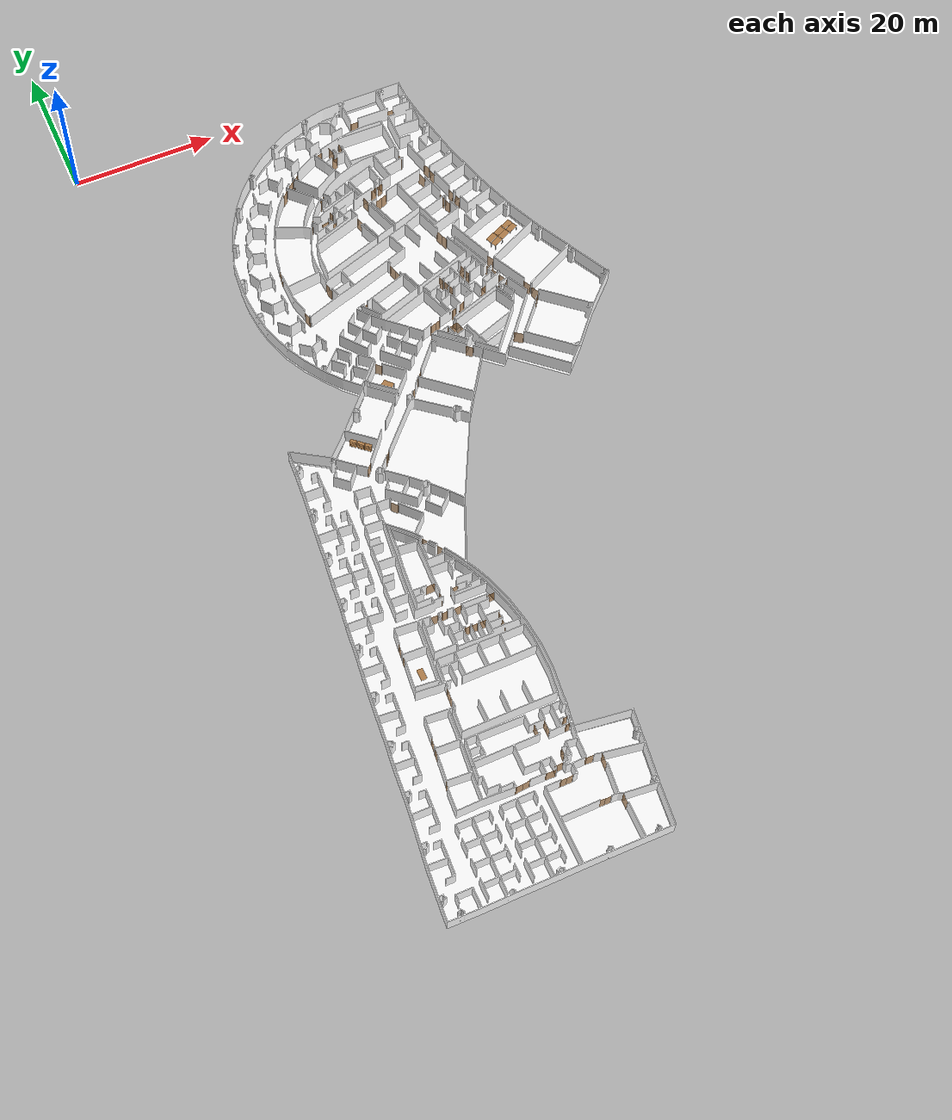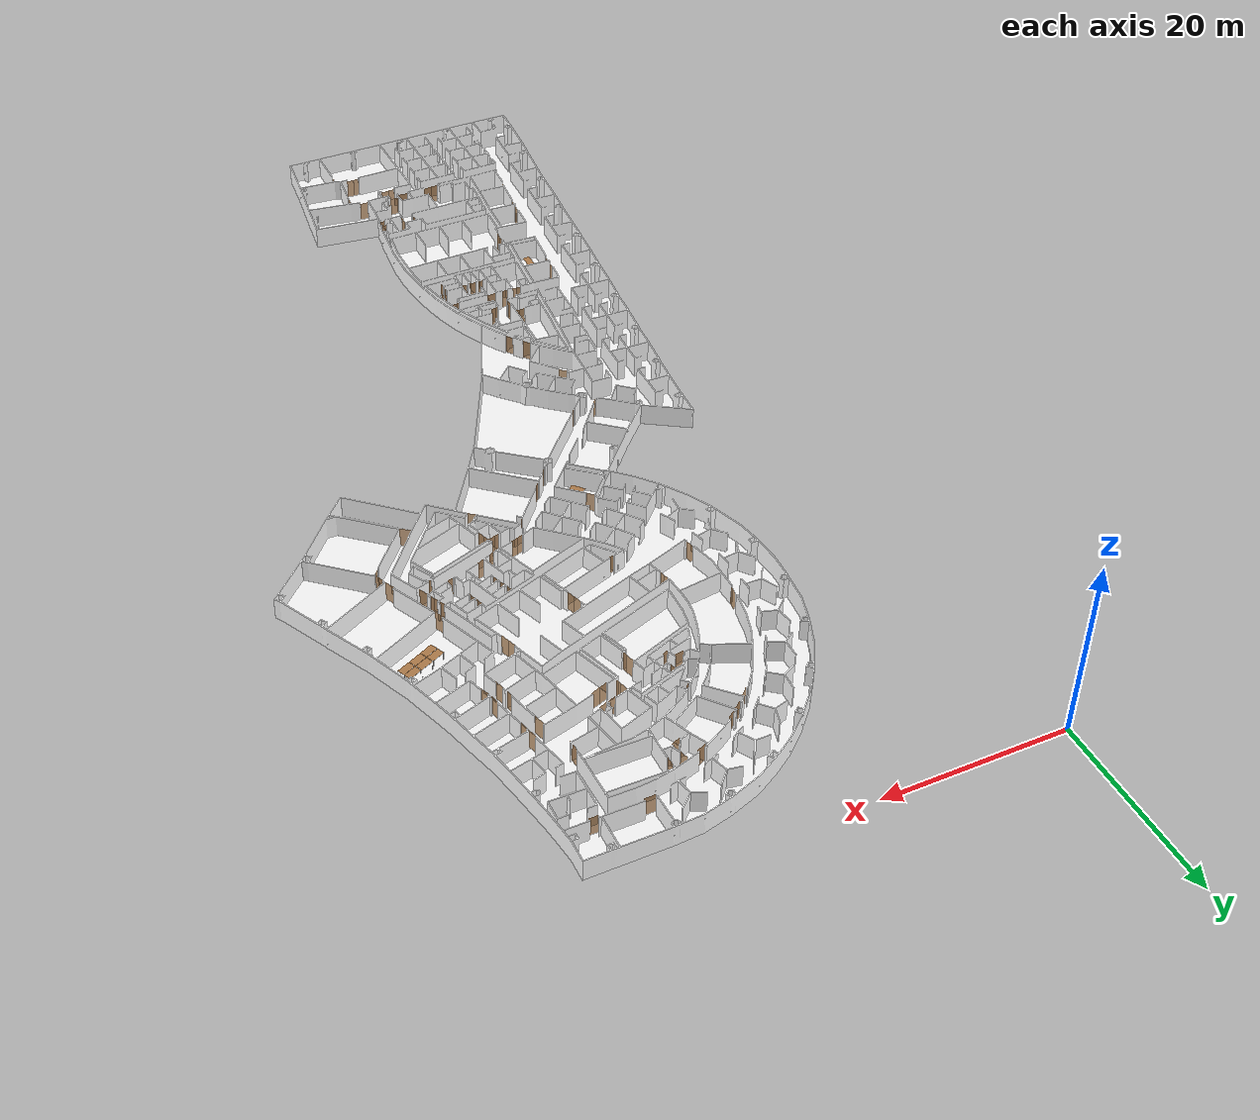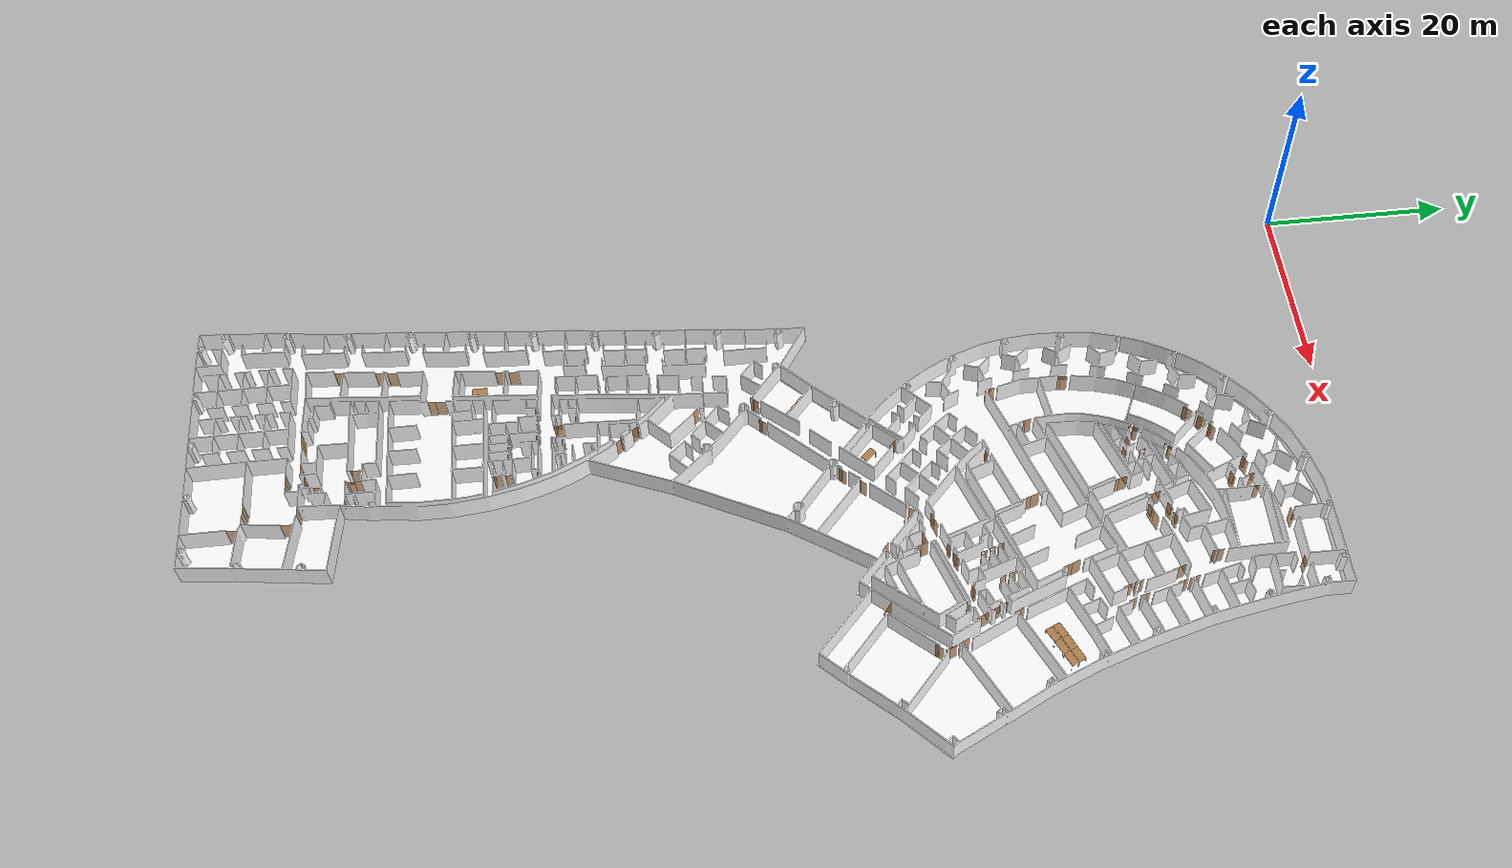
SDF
<sdf version="1.7">
 <world name="world">
  <scene><ambient>0.8 0.8 0.8 1.0</ambient><background>0 0 0</background><grid>false</grid></scene>
  <include><uri>model://sun</uri></include>
  <include>
   <name>OpenRobotics/Table</name>
   <uri>model://Table</uri>
   <pose>14.387834901444366 -87.66442924092927 0.0 0 0 1.5708</pose>
   <static>True</static>
  </include>
  <include>
   <name>OpenRobotics/Table_2</name>
   <uri>model://Table</uri>
   <pose>26.79635193805182 -48.15017493760627 0.0 0 0 2.3292</pose>
   <static>True</static>
  </include>
  <include>
   <name>OpenRobotics/Table_3</name>
   <uri>model://Table</uri>
   <pose>49.11869046079212 -32.151359632969715 0.0 0 0 0.4303</pose>
   <static>True</static>
  </include>
  <include>
   <name>OpenRobotics/Table_4</name>
   <uri>model://Table</uri>
   <pose>50.516762968333715 -31.527827457209188 0.0 0 0 0.4167</pose>
   <static>True</static>
  </include>
  <include>
   <name>OpenRobotics/Table_5</name>
   <uri>model://Table</uri>
   <pose>51.92469862120098 -30.894205397149992 0.0 0 0 0.4347</pose>
   <static>True</static>
  </include>
  <include>
   <name>OpenRobotics/Table_6</name>
   <uri>model://Table</uri>
   <pose>52.26673436197726 -31.64845259084722 0.0 0 0 0.4389</pose>
   <static>True</static>
  </include>
  <include>
   <name>OpenRobotics/Table_7</name>
   <uri>model://Table</uri>
   <pose>50.85868533962349 -32.28207465090642 0.0 0 0 0.4288</pose>
   <static>True</static>
  </include>
  <include>
   <name>OpenRobotics/Table_8</name>
   <uri>model://Table</uri>
   <pose>49.48079260067924 -32.93587647956295 0.0 0 0 0.4547</pose>
   <static>True</static>
  </include>
  <include>
   <name>OpenRobotics/Bookshelf</name>
   <uri>model://Bookshelf</uri>
   <pose>19.416111736263744 -54.29922251598357 0.0 0 0 -0.7204</pose>
   <static>True</static>
  </include>
  <include>
   <name>OpenRobotics/Bookshelf_2</name>
   <uri>model://Bookshelf</uri>
   <pose>20.179881966827136 -54.94622217544999 0.0 0 0 -0.7282</pose>
   <static>True</static>
  </include>
  <include>
   <name>OpenRobotics/Bookshelf_3</name>
   <uri>model://Bookshelf</uri>
   <pose>20.943652197390527 -55.603991936134086 0.0 0 0 -0.7114</pose>
   <static>True</static>
  </include>
  <model name="D1">
   <pose>46.73401999696762 -38.116521904240905 0.0 0 0 -1.0989798712124268</pose>
   <link name="right">
    <pose>0 0 1.11 0 0 0</pose>
    <visual name="right_visual">
     <geometry><box><size>0.9954726975178174 0.03 2.2</size></box></geometry>
     <material><ambient>0.5 0.25 0 0.6</ambient><diffuse>0.5 0.25 0 0.6</diffuse></material>
    </visual>
    <collision name="right_collision">
     <geometry><box><size>0.9954726975178174 0.03 2.2</size></box></geometry>
     <surface><contact><collide_bitmask>0x02</collide_bitmask></contact></surface>
    </collision>
    <inertial>
     <mass>50.0</mass>
     <inertia><ixx>20.17041666666667</ixx><iyy>24.295691214597504</iyy><izz>4.1327745479308335</izz></inertia>
    </inertial>
   </link>
   <joint name="right_joint" type="revolute">
    <parent>world</parent>
    <child>right</child>
    <axis><xyz>0 0 1</xyz><limit><lower>0</lower><upper>1.57</upper></limit></axis>
    <pose>0.5027363487589087 0 0 0 0 0</pose>
   </joint>
   <plugin name="door" filename="libdoor.so">
    <v_max_door>0.5</v_max_door>
    <a_max_door>0.3</a_max_door>
    <a_nom_door>0.15</a_nom_door>
    <dx_min_door>0.01</dx_min_door>
    <f_max_door>500.0</f_max_door>
    <door name="D1" type="SwingDoor" left_joint_name="empty_joint" right_joint_name="right_joint"/>
   </plugin>
  </model>
  <model name="D2">
   <pose>40.57953068323823 -41.08844630814532 0.0 0 0 -2.7133549531312453</pose>
   <link name="right">
    <pose>0 0 1.11 0 0 0</pose>
    <visual name="right_visual">
     <geometry><box><size>0.9223052336505654 0.03 2.2</size></box></geometry>
     <material><ambient>0.5 0.25 0 0.6</ambient><diffuse>0.5 0.25 0 0.6</diffuse></material>
    </visual>
    <collision name="right_collision">
     <geometry><box><size>0.9223052336505654 0.03 2.2</size></box></geometry>
     <surface><contact><collide_bitmask>0x02</collide_bitmask></contact></surface>
    </collision>
    <inertial>
     <mass>50.0</mass>
     <inertia><ixx>20.17041666666667</ixx><iyy>23.711028933413438</iyy><izz>3.548112266746767</izz></inertia>
    </inertial>
   </link>
   <joint name="right_joint" type="revolute">
    <parent>world</parent>
    <child>right</child>
    <axis><xyz>0 0 1</xyz><limit><lower>0</lower><upper>1.57</upper></limit></axis>
    <pose>0.4661526168252827 0 0 0 0 0</pose>
   </joint>
   <plugin name="door" filename="libdoor.so">
    <v_max_door>0.5</v_max_door>
    <a_max_door>0.3</a_max_door>
    <a_nom_door>0.15</a_nom_door>
    <dx_min_door>0.01</dx_min_door>
    <f_max_door>500.0</f_max_door>
    <door name="D2" type="SwingDoor" left_joint_name="empty_joint" right_joint_name="right_joint"/>
   </plugin>
  </model>
  <model name="D3">
   <pose>44.28064762432295 -39.935648684650616 0.0 0 0 -2.8085231029714617</pose>
   <link name="right">
    <pose>0 0 1.11 0 0 0</pose>
    <visual name="right_visual">
     <geometry><box><size>0.8388526958667103 0.03 2.2</size></box></geometry>
     <material><ambient>0.5 0.25 0 0.6</ambient><diffuse>0.5 0.25 0 0.6</diffuse></material>
    </visual>
    <collision name="right_collision">
     <geometry><box><size>0.8388526958667103 0.03 2.2</size></box></geometry>
     <surface><contact><collide_bitmask>0x02</collide_bitmask></contact></surface>
    </collision>
    <inertial>
     <mass>50.0</mass>
     <inertia><ixx>20.17041666666667</ixx><iyy>23.098641022345202</iyy><izz>2.935724355678532</izz></inertia>
    </inertial>
   </link>
   <joint name="right_joint" type="revolute">
    <parent>world</parent>
    <child>right</child>
    <axis><xyz>0 0 1</xyz><limit><lower>0</lower><upper>1.57</upper></limit></axis>
    <pose>0.42442634793335515 0 0 0 0 0</pose>
   </joint>
   <plugin name="door" filename="libdoor.so">
    <v_max_door>0.5</v_max_door>
    <a_max_door>0.3</a_max_door>
    <a_nom_door>0.15</a_nom_door>
    <dx_min_door>0.01</dx_min_door>
    <f_max_door>500.0</f_max_door>
    <door name="D3" type="SwingDoor" left_joint_name="empty_joint" right_joint_name="right_joint"/>
   </plugin>
  </model>
  <model name="D4">
   <pose>46.26773129898525 -37.17578190524803 0.0 0 0 -1.0969033267898198</pose>
   <link name="right">
    <pose>0 0 1.11 0 0 0</pose>
    <visual name="right_visual">
     <geometry><box><size>0.6729192020442292 0.03 2.2</size></box></geometry>
     <material><ambient>0.5 0.25 0 0.6</ambient><diffuse>0.5 0.25 0 0.6</diffuse></material>
    </visual>
    <collision name="right_collision">
     <geometry><box><size>0.6729192020442292 0.03 2.2</size></box></geometry>
     <surface><contact><collide_bitmask>0x02</collide_bitmask></contact></surface>
    </collision>
    <inertial>
     <mass>50.0</mass>
     <inertia><ixx>20.17041666666667</ixx><iyy>22.053417718666015</iyy><izz>1.8905010519993424</izz></inertia>
    </inertial>
   </link>
   <joint name="right_joint" type="revolute">
    <parent>world</parent>
    <child>right</child>
    <axis><xyz>0 0 1</xyz><limit><lower>0</lower><upper>1.57</upper></limit></axis>
    <pose>0.3414596010221146 0 0 0 0 0</pose>
   </joint>
   <plugin name="door" filename="libdoor.so">
    <v_max_door>0.5</v_max_door>
    <a_max_door>0.3</a_max_door>
    <a_nom_door>0.15</a_nom_door>
    <dx_min_door>0.01</dx_min_door>
    <f_max_door>500.0</f_max_door>
    <door name="D4" type="SwingDoor" left_joint_name="empty_joint" right_joint_name="right_joint"/>
   </plugin>
  </model>
  <model name="D5">
   <pose>47.146061395658826 -35.89175910112735 0.0 0 0 -1.153911512128053</pose>
   <link name="right">
    <pose>0 0 1.11 0 0 0</pose>
    <visual name="right_visual">
     <geometry><box><size>1.107136500225775 0.03 2.2</size></box></geometry>
     <material><ambient>0.5 0.25 0 0.6</ambient><diffuse>0.5 0.25 0 0.6</diffuse></material>
    </visual>
    <collision name="right_collision">
     <geometry><box><size>1.107136500225775 0.03 2.2</size></box></geometry>
     <surface><contact><collide_bitmask>0x02</collide_bitmask></contact></surface>
    </collision>
    <inertial>
     <mass>50.0</mass>
     <inertia><ixx>20.17041666666667</ixx><iyy>25.273963458884076</iyy><izz>5.111046792217405</izz></inertia>
    </inertial>
   </link>
   <joint name="right_joint" type="revolute">
    <parent>world</parent>
    <child>right</child>
    <axis><xyz>0 0 -1</xyz><limit><lower>0</lower><upper>1.57</upper></limit></axis>
    <pose>0.5585682501128875 0 0 0 0 0</pose>
   </joint>
   <plugin name="door" filename="libdoor.so">
    <v_max_door>0.5</v_max_door>
    <a_max_door>0.3</a_max_door>
    <a_nom_door>0.15</a_nom_door>
    <dx_min_door>0.01</dx_min_door>
    <f_max_door>500.0</f_max_door>
    <door name="D5" type="SwingDoor" left_joint_name="empty_joint" right_joint_name="right_joint"/>
   </plugin>
  </model>
  <model name="D6">
   <pose>49.93642456693043 -41.661415692926 0.0 0 0 -1.1319738374537638</pose>
   <link name="right">
    <pose>0 0 1.11 0 0 0</pose>
    <visual name="right_visual">
     <geometry><box><size>1.1848690229402588 0.03 2.2</size></box></geometry>
     <material><ambient>0.5 0.25 0 0.6</ambient><diffuse>0.5 0.25 0 0.6</diffuse></material>
    </visual>
    <collision name="right_collision">
     <geometry><box><size>1.1848690229402588 0.03 2.2</size></box></geometry>
     <surface><contact><collide_bitmask>0x02</collide_bitmask></contact></surface>
    </collision>
    <inertial>
     <mass>50.0</mass>
     <inertia><ixx>20.17041666666667</ixx><iyy>26.016310839680852</iyy><izz>5.8533941730141805</izz></inertia>
    </inertial>
   </link>
   <joint name="right_joint" type="revolute">
    <parent>world</parent>
    <child>right</child>
    <axis><xyz>0 0 -1</xyz><limit><lower>0</lower><upper>1.57</upper></limit></axis>
    <pose>0.5974345114701294 0 0 0 0 0</pose>
   </joint>
   <plugin name="door" filename="libdoor.so">
    <v_max_door>0.5</v_max_door>
    <a_max_door>0.3</a_max_door>
    <a_nom_door>0.15</a_nom_door>
    <dx_min_door>0.01</dx_min_door>
    <f_max_door>500.0</f_max_door>
    <door name="D6" type="SwingDoor" left_joint_name="empty_joint" right_joint_name="right_joint"/>
   </plugin>
  </model>
  <model name="D7">
   <pose>50.496809938709376 -42.986478251160364 0.0 0 0 -1.1821076421310168</pose>
   <link name="right">
    <pose>0 0 1.11 0 0 0</pose>
    <visual name="right_visual">
     <geometry><box><size>1.2147097628810168 0.03 2.2</size></box></geometry>
     <material><ambient>0.5 0.25 0 0.6</ambient><diffuse>0.5 0.25 0 0.6</diffuse></material>
    </visual>
    <collision name="right_collision">
     <geometry><box><size>1.2147097628810168 0.03 2.2</size></box></geometry>
     <surface><contact><collide_bitmask>0x02</collide_bitmask></contact></surface>
    </collision>
    <inertial>
     <mass>50.0</mass>
     <inertia><ixx>20.17041666666667</ixx><iyy>26.314665866826903</iyy><izz>6.151749200160234</izz></inertia>
    </inertial>
   </link>
   <joint name="right_joint" type="revolute">
    <parent>world</parent>
    <child>right</child>
    <axis><xyz>0 0 1</xyz><limit><lower>0</lower><upper>1.57</upper></limit></axis>
    <pose>0.6123548814405084 0 0 0 0 0</pose>
   </joint>
   <plugin name="door" filename="libdoor.so">
    <v_max_door>0.5</v_max_door>
    <a_max_door>0.3</a_max_door>
    <a_nom_door>0.15</a_nom_door>
    <dx_min_door>0.01</dx_min_door>
    <f_max_door>500.0</f_max_door>
    <door name="D7" type="SwingDoor" left_joint_name="empty_joint" right_joint_name="right_joint"/>
   </plugin>
  </model>
  <model name="D8">
   <pose>50.31558881453607 -44.061107613712 0.0 0 0 0.8936867215143733</pose>
   <link name="right">
    <pose>0 0 1.11 0 0 0</pose>
    <visual name="right_visual">
     <geometry><box><size>0.9542531826486202 0.03 2.2</size></box></geometry>
     <material><ambient>0.5 0.25 0 0.6</ambient><diffuse>0.5 0.25 0 0.6</diffuse></material>
    </visual>
    <collision name="right_collision">
     <geometry><box><size>0.9542531826486202 0.03 2.2</size></box></geometry>
     <surface><contact><collide_bitmask>0x02</collide_bitmask></contact></surface>
    </collision>
    <inertial>
     <mass>50.0</mass>
     <inertia><ixx>20.17041666666667</ixx><iyy>23.96082973581259</iyy><izz>3.7979130691459213</izz></inertia>
    </inertial>
   </link>
   <joint name="right_joint" type="revolute">
    <parent>world</parent>
    <child>right</child>
    <axis><xyz>0 0 1</xyz><limit><lower>0</lower><upper>1.57</upper></limit></axis>
    <pose>0.4821265913243101 0 0 0 0 0</pose>
   </joint>
   <plugin name="door" filename="libdoor.so">
    <v_max_door>0.5</v_max_door>
    <a_max_door>0.3</a_max_door>
    <a_nom_door>0.15</a_nom_door>
    <dx_min_door>0.01</dx_min_door>
    <f_max_door>500.0</f_max_door>
    <door name="D8" type="SwingDoor" left_joint_name="empty_joint" right_joint_name="right_joint"/>
   </plugin>
  </model>
  <model name="D9">
   <pose>45.54562435471131 -48.47684911296154 0.0 0 0 2.500232906125346</pose>
   <link name="right">
    <pose>0 0 1.11 0 0 0</pose>
    <visual name="right_visual">
     <geometry><box><size>1.3029803812608298 0.03 2.2</size></box></geometry>
     <material><ambient>0.5 0.25 0 0.6</ambient><diffuse>0.5 0.25 0 0.6</diffuse></material>
    </visual>
    <collision name="right_collision">
     <geometry><box><size>1.3029803812608298 0.03 2.2</size></box></geometry>
     <surface><contact><collide_bitmask>0x02</collide_bitmask></contact></surface>
    </collision>
    <inertial>
     <mass>50.0</mass>
     <inertia><ixx>20.17041666666667</ixx><iyy>27.240657808127576</iyy><izz>7.077741141460906</izz></inertia>
    </inertial>
   </link>
   <joint name="right_joint" type="revolute">
    <parent>world</parent>
    <child>right</child>
    <axis><xyz>0 0 -1</xyz><limit><lower>0</lower><upper>1.57</upper></limit></axis>
    <pose>0.6564901906304149 0 0 0 0 0</pose>
   </joint>
   <plugin name="door" filename="libdoor.so">
    <v_max_door>0.5</v_max_door>
    <a_max_door>0.3</a_max_door>
    <a_nom_door>0.15</a_nom_door>
    <dx_min_door>0.01</dx_min_door>
    <f_max_door>500.0</f_max_door>
    <door name="D9" type="SwingDoor" left_joint_name="empty_joint" right_joint_name="right_joint"/>
   </plugin>
  </model>
  <model name="D10">
   <pose>47.383400415650584 -39.50030985648326 0.0 0 0 -1.079641047657817</pose>
   <link name="right">
    <pose>0 0 1.11 0 0 0</pose>
    <visual name="right_visual">
     <geometry><box><size>1.387273254949858 0.03 2.2</size></box></geometry>
     <material><ambient>0.5 0.25 0 0.6</ambient><diffuse>0.5 0.25 0 0.6</diffuse></material>
    </visual>
    <collision name="right_collision">
     <geometry><box><size>1.387273254949858 0.03 2.2</size></box></geometry>
     <surface><contact><collide_bitmask>0x02</collide_bitmask></contact></surface>
    </collision>
    <inertial>
     <mass>50.0</mass>
     <inertia><ixx>20.17041666666667</ixx><iyy>28.185529516246564</iyy><izz>8.022612849579891</izz></inertia>
    </inertial>
   </link>
   <joint name="right_joint" type="revolute">
    <parent>world</parent>
    <child>right</child>
    <axis><xyz>0 0 1</xyz><limit><lower>0</lower><upper>1.57</upper></limit></axis>
    <pose>0.698636627474929 0 0 0 0 0</pose>
   </joint>
   <plugin name="door" filename="libdoor.so">
    <v_max_door>0.5</v_max_door>
    <a_max_door>0.3</a_max_door>
    <a_nom_door>0.15</a_nom_door>
    <dx_min_door>0.01</dx_min_door>
    <f_max_door>500.0</f_max_door>
    <door name="D10" type="SwingDoor" left_joint_name="empty_joint" right_joint_name="right_joint"/>
   </plugin>
  </model>
  <model name="D11">
   <pose>45.99190333832609 -40.67419420446733 0.0 0 0 0.39306529233235726</pose>
   <link name="right">
    <pose>0 0 1.11 0 0 0</pose>
    <visual name="right_visual">
     <geometry><box><size>0.6923773392659476 0.03 2.2</size></box></geometry>
     <material><ambient>0.5 0.25 0 0.6</ambient><diffuse>0.5 0.25 0 0.6</diffuse></material>
    </visual>
    <collision name="right_collision">
     <geometry><box><size>0.6923773392659476 0.03 2.2</size></box></geometry>
     <surface><contact><collide_bitmask>0x02</collide_bitmask></contact></surface>
    </collision>
    <inertial>
     <mass>50.0</mass>
     <inertia><ixx>20.17041666666667</ixx><iyy>22.16410991637081</iyy><izz>2.001193249704138</izz></inertia>
    </inertial>
   </link>
   <joint name="right_joint" type="revolute">
    <parent>world</parent>
    <child>right</child>
    <axis><xyz>0 0 1</xyz><limit><lower>0</lower><upper>1.57</upper></limit></axis>
    <pose>0.3511886696329738 0 0 0 0 0</pose>
   </joint>
   <plugin name="door" filename="libdoor.so">
    <v_max_door>0.5</v_max_door>
    <a_max_door>0.3</a_max_door>
    <a_nom_door>0.15</a_nom_door>
    <dx_min_door>0.01</dx_min_door>
    <f_max_door>500.0</f_max_door>
    <door name="D11" type="SwingDoor" left_joint_name="empty_joint" right_joint_name="right_joint"/>
   </plugin>
  </model>
  <model name="D12">
   <pose>47.22224569058811 -24.82995819467613 0.0 0 0 -1.206774434324264</pose>
   <link name="right">
    <pose>0 0 1.11 0 0 0</pose>
    <visual name="right_visual">
     <geometry><box><size>0.9299814647233979 0.03 2.2</size></box></geometry>
     <material><ambient>0.5 0.25 0 0.6</ambient><diffuse>0.5 0.25 0 0.6</diffuse></material>
    </visual>
    <collision name="right_collision">
     <geometry><box><size>0.9299814647233979 0.03 2.2</size></box></geometry>
     <surface><contact><collide_bitmask>0x02</collide_bitmask></contact></surface>
    </collision>
    <inertial>
     <mass>50.0</mass>
     <inertia><ixx>20.17041666666667</ixx><iyy>23.770273019704494</iyy><izz>3.6073563530378197</izz></inertia>
    </inertial>
   </link>
   <joint name="right_joint" type="revolute">
    <parent>world</parent>
    <child>right</child>
    <axis><xyz>0 0 1</xyz><limit><lower>0</lower><upper>1.57</upper></limit></axis>
    <pose>0.46999073236169897 0 0 0 0 0</pose>
   </joint>
   <plugin name="door" filename="libdoor.so">
    <v_max_door>0.5</v_max_door>
    <a_max_door>0.3</a_max_door>
    <a_nom_door>0.15</a_nom_door>
    <dx_min_door>0.01</dx_min_door>
    <f_max_door>500.0</f_max_door>
    <door name="D12" type="SwingDoor" left_joint_name="empty_joint" right_joint_name="right_joint"/>
   </plugin>
  </model>
  <model name="D13">
   <pose>46.78605659127199 -23.541003817892623 0.0 0 0 -1.3188596632420009</pose>
   <link name="right">
    <pose>0 0 1.11 0 0 0</pose>
    <visual name="right_visual">
     <geometry><box><size>0.981892242367588 0.03 2.2</size></box></geometry>
     <material><ambient>0.5 0.25 0 0.6</ambient><diffuse>0.5 0.25 0 0.6</diffuse></material>
    </visual>
    <collision name="right_collision">
     <geometry><box><size>0.981892242367588 0.03 2.2</size></box></geometry>
     <surface><contact><collide_bitmask>0x02</collide_bitmask></contact></surface>
    </collision>
    <inertial>
     <mass>50.0</mass>
     <inertia><ixx>20.17041666666667</ixx><iyy>24.183801565090214</iyy><izz>4.020884898423543</izz></inertia>
    </inertial>
   </link>
   <joint name="right_joint" type="revolute">
    <parent>world</parent>
    <child>right</child>
    <axis><xyz>0 0 -1</xyz><limit><lower>0</lower><upper>1.57</upper></limit></axis>
    <pose>0.495946121183794 0 0 0 0 0</pose>
   </joint>
   <plugin name="door" filename="libdoor.so">
    <v_max_door>0.5</v_max_door>
    <a_max_door>0.3</a_max_door>
    <a_nom_door>0.15</a_nom_door>
    <dx_min_door>0.01</dx_min_door>
    <f_max_door>500.0</f_max_door>
    <door name="D13" type="SwingDoor" left_joint_name="empty_joint" right_joint_name="right_joint"/>
   </plugin>
  </model>
  <model name="D14">
   <pose>45.705815439138505 -19.567913478689803 0.0 0 0 -1.3543970765350084</pose>
   <link name="right">
    <pose>0 0 1.11 0 0 0</pose>
    <visual name="right_visual">
     <geometry><box><size>0.9868671713911081 0.03 2.2</size></box></geometry>
     <material><ambient>0.5 0.25 0 0.6</ambient><diffuse>0.5 0.25 0 0.6</diffuse></material>
    </visual>
    <collision name="right_collision">
     <geometry><box><size>0.9868671713911081 0.03 2.2</size></box></geometry>
     <surface><contact><collide_bitmask>0x02</collide_bitmask></contact></surface>
    </collision>
    <inertial>
     <mass>50.0</mass>
     <inertia><ixx>20.17041666666667</ixx><iyy>24.224611724872865</iyy><izz>4.061695058206195</izz></inertia>
    </inertial>
   </link>
   <joint name="right_joint" type="revolute">
    <parent>world</parent>
    <child>right</child>
    <axis><xyz>0 0 1</xyz><limit><lower>0</lower><upper>1.57</upper></limit></axis>
    <pose>0.49843358569555407 0 0 0 0 0</pose>
   </joint>
   <plugin name="door" filename="libdoor.so">
    <v_max_door>0.5</v_max_door>
    <a_max_door>0.3</a_max_door>
    <a_nom_door>0.15</a_nom_door>
    <dx_min_door>0.01</dx_min_door>
    <f_max_door>500.0</f_max_door>
    <door name="D14" type="SwingDoor" left_joint_name="empty_joint" right_joint_name="right_joint"/>
   </plugin>
  </model>
  <model name="D15">
   <pose>45.407937113354734 -18.323059832155543 0.0 0 0 -1.2966441673642015</pose>
   <link name="right">
    <pose>0 0 1.11 0 0 0</pose>
    <visual name="right_visual">
     <geometry><box><size>1.1051405002353125 0.03 2.2</size></box></geometry>
     <material><ambient>0.5 0.25 0 0.6</ambient><diffuse>0.5 0.25 0 0.6</diffuse></material>
    </visual>
    <collision name="right_collision">
     <geometry><box><size>1.1051405002353125 0.03 2.2</size></box></geometry>
     <surface><contact><collide_bitmask>0x02</collide_bitmask></contact></surface>
    </collision>
    <inertial>
     <mass>50.0</mass>
     <inertia><ixx>20.17041666666667</ixx><iyy>25.255564688584826</iyy><izz>5.092648021918153</izz></inertia>
    </inertial>
   </link>
   <joint name="right_joint" type="revolute">
    <parent>world</parent>
    <child>right</child>
    <axis><xyz>0 0 -1</xyz><limit><lower>0</lower><upper>1.57</upper></limit></axis>
    <pose>0.5575702501176563 0 0 0 0 0</pose>
   </joint>
   <plugin name="door" filename="libdoor.so">
    <v_max_door>0.5</v_max_door>
    <a_max_door>0.3</a_max_door>
    <a_nom_door>0.15</a_nom_door>
    <dx_min_door>0.01</dx_min_door>
    <f_max_door>500.0</f_max_door>
    <door name="D15" type="SwingDoor" left_joint_name="empty_joint" right_joint_name="right_joint"/>
   </plugin>
  </model>
  <model name="D16">
   <pose>42.667853309346725 -15.418760326949517 0.0 0 0 -1.4795248715580769</pose>
   <link name="right">
    <pose>0 0 1.11 0 0 0</pose>
    <visual name="right_visual">
     <geometry><box><size>1.1815982625001065 0.03 2.2</size></box></geometry>
     <material><ambient>0.5 0.25 0 0.6</ambient><diffuse>0.5 0.25 0 0.6</diffuse></material>
    </visual>
    <collision name="right_collision">
     <geometry><box><size>1.1815982625001065 0.03 2.2</size></box></geometry>
     <surface><contact><collide_bitmask>0x02</collide_bitmask></contact></surface>
    </collision>
    <inertial>
     <mass>50.0</mass>
     <inertia><ixx>20.17041666666667</ixx><iyy>25.984060224763635</iyy><izz>5.821143558096961</izz></inertia>
    </inertial>
   </link>
   <joint name="right_joint" type="revolute">
    <parent>world</parent>
    <child>right</child>
    <axis><xyz>0 0 1</xyz><limit><lower>0</lower><upper>1.57</upper></limit></axis>
    <pose>0.5957991312500532 0 0 0 0 0</pose>
   </joint>
   <plugin name="door" filename="libdoor.so">
    <v_max_door>0.5</v_max_door>
    <a_max_door>0.3</a_max_door>
    <a_nom_door>0.15</a_nom_door>
    <dx_min_door>0.01</dx_min_door>
    <f_max_door>500.0</f_max_door>
    <door name="D16" type="SwingDoor" left_joint_name="empty_joint" right_joint_name="right_joint"/>
   </plugin>
  </model>
  <model name="D17">
   <pose>44.15061282330526 -19.557256746958622 0.0 0 0 1.8422869865588756</pose>
   <link name="right">
    <pose>0 0 1.11 0 0 0</pose>
    <visual name="right_visual">
     <geometry><box><size>1.2844782149061784 0.03 2.2</size></box></geometry>
     <material><ambient>0.5 0.25 0 0.6</ambient><diffuse>0.5 0.25 0 0.6</diffuse></material>
    </visual>
    <collision name="right_collision">
     <geometry><box><size>1.2844782149061784 0.03 2.2</size></box></geometry>
     <surface><contact><collide_bitmask>0x02</collide_bitmask></contact></surface>
    </collision>
    <inertial>
     <mass>50.0</mass>
     <inertia><ixx>20.17041666666667</ixx><iyy>27.04118451903568</iyy><izz>6.878267852369011</izz></inertia>
    </inertial>
   </link>
   <joint name="right_joint" type="revolute">
    <parent>world</parent>
    <child>right</child>
    <axis><xyz>0 0 -1</xyz><limit><lower>0</lower><upper>1.57</upper></limit></axis>
    <pose>0.6472391074530892 0 0 0 0 0</pose>
   </joint>
   <plugin name="door" filename="libdoor.so">
    <v_max_door>0.5</v_max_door>
    <a_max_door>0.3</a_max_door>
    <a_nom_door>0.15</a_nom_door>
    <dx_min_door>0.01</dx_min_door>
    <f_max_door>500.0</f_max_door>
    <door name="D17" type="SwingDoor" left_joint_name="empty_joint" right_joint_name="right_joint"/>
   </plugin>
  </model>
  <model name="D18">
   <pose>45.29388740993381 -23.83077622539151 0.0 0 0 1.8423285281827284</pose>
   <link name="right">
    <pose>0 0 1.11 0 0 0</pose>
    <visual name="right_visual">
     <geometry><box><size>0.9541620605206925 0.03 2.2</size></box></geometry>
     <material><ambient>0.5 0.25 0 0.6</ambient><diffuse>0.5 0.25 0 0.6</diffuse></material>
    </visual>
    <collision name="right_collision">
     <geometry><box><size>0.9541620605206925 0.03 2.2</size></box></geometry>
     <surface><contact><collide_bitmask>0x02</collide_bitmask></contact></surface>
    </collision>
    <inertial>
     <mass>50.0</mass>
     <inertia><ixx>20.17041666666667</ixx><iyy>23.960105157237898</iyy><izz>3.7971884905712243</izz></inertia>
    </inertial>
   </link>
   <joint name="right_joint" type="revolute">
    <parent>world</parent>
    <child>right</child>
    <axis><xyz>0 0 1</xyz><limit><lower>0</lower><upper>1.57</upper></limit></axis>
    <pose>0.48208103026034627 0 0 0 0 0</pose>
   </joint>
   <plugin name="door" filename="libdoor.so">
    <v_max_door>0.5</v_max_door>
    <a_max_door>0.3</a_max_door>
    <a_nom_door>0.15</a_nom_door>
    <dx_min_door>0.01</dx_min_door>
    <f_max_door>500.0</f_max_door>
    <door name="D18" type="SwingDoor" left_joint_name="empty_joint" right_joint_name="right_joint"/>
   </plugin>
  </model>
  <model name="D19">
   <pose>45.64737346884678 -25.03254946705505 0.0 0 0 1.9038844260786356</pose>
   <link name="right">
    <pose>0 0 1.11 0 0 0</pose>
    <visual name="right_visual">
     <geometry><box><size>0.9924107750822058 0.03 2.2</size></box></geometry>
     <material><ambient>0.5 0.25 0 0.6</ambient><diffuse>0.5 0.25 0 0.6</diffuse></material>
    </visual>
    <collision name="right_collision">
     <geometry><box><size>0.9924107750822058 0.03 2.2</size></box></geometry>
     <surface><contact><collide_bitmask>0x02</collide_bitmask></contact></surface>
    </collision>
    <inertial>
     <mass>50.0</mass>
     <inertia><ixx>20.17041666666667</ixx><iyy>24.270329777080274</iyy><izz>4.107413110413602</izz></inertia>
    </inertial>
   </link>
   <joint name="right_joint" type="revolute">
    <parent>world</parent>
    <child>right</child>
    <axis><xyz>0 0 -1</xyz><limit><lower>0</lower><upper>1.57</upper></limit></axis>
    <pose>0.5012053875411029 0 0 0 0 0</pose>
   </joint>
   <plugin name="door" filename="libdoor.so">
    <v_max_door>0.5</v_max_door>
    <a_max_door>0.3</a_max_door>
    <a_nom_door>0.15</a_nom_door>
    <dx_min_door>0.01</dx_min_door>
    <f_max_door>500.0</f_max_door>
    <door name="D19" type="SwingDoor" left_joint_name="empty_joint" right_joint_name="right_joint"/>
   </plugin>
  </model>
  <model name="D20">
   <pose>40.27808121862964 -38.281474507101194 0.0 0 0 -1.2252226117643752</pose>
   <link name="right">
    <pose>0 0 1.11 0 0 0</pose>
    <visual name="right_visual">
     <geometry><box><size>0.6958472451859321 0.03 2.2</size></box></geometry>
     <material><ambient>0.5 0.25 0 0.6</ambient><diffuse>0.5 0.25 0 0.6</diffuse></material>
    </visual>
    <collision name="right_collision">
     <geometry><box><size>0.6958472451859321 0.03 2.2</size></box></geometry>
     <surface><contact><collide_bitmask>0x02</collide_bitmask></contact></surface>
    </collision>
    <inertial>
     <mass>50.0</mass>
     <inertia><ixx>20.17041666666667</ixx><iyy>22.184180785970213</iyy><izz>2.0212641193035448</izz></inertia>
    </inertial>
   </link>
   <joint name="right_joint" type="revolute">
    <parent>world</parent>
    <child>right</child>
    <axis><xyz>0 0 1</xyz><limit><lower>0</lower><upper>1.57</upper></limit></axis>
    <pose>0.35292362259296606 0 0 0 0 0</pose>
   </joint>
   <plugin name="door" filename="libdoor.so">
    <v_max_door>0.5</v_max_door>
    <a_max_door>0.3</a_max_door>
    <a_nom_door>0.15</a_nom_door>
    <dx_min_door>0.01</dx_min_door>
    <f_max_door>500.0</f_max_door>
    <door name="D20" type="SwingDoor" left_joint_name="empty_joint" right_joint_name="right_joint"/>
   </plugin>
  </model>
  <model name="D21">
   <pose>39.939900040394434 -37.37491540828863 0.0 0 0 -1.1737168815699124</pose>
   <link name="right">
    <pose>0 0 1.11 0 0 0</pose>
    <visual name="right_visual">
     <geometry><box><size>0.6797853655331796 0.03 2.2</size></box></geometry>
     <material><ambient>0.5 0.25 0 0.6</ambient><diffuse>0.5 0.25 0 0.6</diffuse></material>
    </visual>
    <collision name="right_collision">
     <geometry><box><size>0.6797853655331796 0.03 2.2</size></box></geometry>
     <surface><contact><collide_bitmask>0x02</collide_bitmask></contact></surface>
    </collision>
    <inertial>
     <mass>50.0</mass>
     <inertia><ixx>20.17041666666667</ixx><iyy>22.092117263304498</iyy><izz>1.9292005966378276</izz></inertia>
    </inertial>
   </link>
   <joint name="right_joint" type="revolute">
    <parent>world</parent>
    <child>right</child>
    <axis><xyz>0 0 1</xyz><limit><lower>0</lower><upper>1.57</upper></limit></axis>
    <pose>0.3448926827665898 0 0 0 0 0</pose>
   </joint>
   <plugin name="door" filename="libdoor.so">
    <v_max_door>0.5</v_max_door>
    <a_max_door>0.3</a_max_door>
    <a_nom_door>0.15</a_nom_door>
    <dx_min_door>0.01</dx_min_door>
    <f_max_door>500.0</f_max_door>
    <door name="D21" type="SwingDoor" left_joint_name="empty_joint" right_joint_name="right_joint"/>
   </plugin>
  </model>
  <model name="D22">
   <pose>39.6094846719846 -36.50678856540023 0.0 0 0 -1.2232855965163583</pose>
   <link name="right">
    <pose>0 0 1.11 0 0 0</pose>
    <visual name="right_visual">
     <geometry><box><size>0.6970646108049134 0.03 2.2</size></box></geometry>
     <material><ambient>0.5 0.25 0 0.6</ambient><diffuse>0.5 0.25 0 0.6</diffuse></material>
    </visual>
    <collision name="right_collision">
     <geometry><box><size>0.6970646108049134 0.03 2.2</size></box></geometry>
     <surface><contact><collide_bitmask>0x02</collide_bitmask></contact></surface>
    </collision>
    <inertial>
     <mass>50.0</mass>
     <inertia><ixx>20.17041666666667</ixx><iyy>22.191246131819195</iyy><izz>2.028329465152523</izz></inertia>
    </inertial>
   </link>
   <joint name="right_joint" type="revolute">
    <parent>world</parent>
    <child>right</child>
    <axis><xyz>0 0 1</xyz><limit><lower>0</lower><upper>1.57</upper></limit></axis>
    <pose>0.3535323054024567 0 0 0 0 0</pose>
   </joint>
   <plugin name="door" filename="libdoor.so">
    <v_max_door>0.5</v_max_door>
    <a_max_door>0.3</a_max_door>
    <a_nom_door>0.15</a_nom_door>
    <dx_min_door>0.01</dx_min_door>
    <f_max_door>500.0</f_max_door>
    <door name="D22" type="SwingDoor" left_joint_name="empty_joint" right_joint_name="right_joint"/>
   </plugin>
  </model>
  <model name="D23">
   <pose>43.31326579600213 -36.8663965765843 0.0 0 0 -1.2084228363325662</pose>
   <link name="right">
    <pose>0 0 1.11 0 0 0</pose>
    <visual name="right_visual">
     <geometry><box><size>0.6750244066471521 0.03 2.2</size></box></geometry>
     <material><ambient>0.5 0.25 0 0.6</ambient><diffuse>0.5 0.25 0 0.6</diffuse></material>
    </visual>
    <collision name="right_collision">
     <geometry><box><size>0.6750244066471521 0.03 2.2</size></box></geometry>
     <surface><contact><collide_bitmask>0x02</collide_bitmask></contact></surface>
    </collision>
    <inertial>
     <mass>50.0</mass>
     <inertia><ixx>20.17041666666667</ixx><iyy>22.06524145653892</iyy><izz>1.9023247898722493</izz></inertia>
    </inertial>
   </link>
   <joint name="right_joint" type="revolute">
    <parent>world</parent>
    <child>right</child>
    <axis><xyz>0 0 1</xyz><limit><lower>0</lower><upper>1.57</upper></limit></axis>
    <pose>0.34251220332357607 0 0 0 0 0</pose>
   </joint>
   <plugin name="door" filename="libdoor.so">
    <v_max_door>0.5</v_max_door>
    <a_max_door>0.3</a_max_door>
    <a_nom_door>0.15</a_nom_door>
    <dx_min_door>0.01</dx_min_door>
    <f_max_door>500.0</f_max_door>
    <door name="D23" type="SwingDoor" left_joint_name="empty_joint" right_joint_name="right_joint"/>
   </plugin>
  </model>
  <model name="D24">
   <pose>42.97706858378069 -35.91165544600844 0.0 0 0 -1.2416042181407223</pose>
   <link name="right">
    <pose>0 0 1.11 0 0 0</pose>
    <visual name="right_visual">
     <geometry><box><size>0.7800969463322023 0.03 2.2</size></box></geometry>
     <material><ambient>0.5 0.25 0 0.6</ambient><diffuse>0.5 0.25 0 0.6</diffuse></material>
    </visual>
    <collision name="right_collision">
     <geometry><box><size>0.7800969463322023 0.03 2.2</size></box></geometry>
     <surface><contact><collide_bitmask>0x02</collide_bitmask></contact></surface>
    </collision>
    <inertial>
     <mass>50.0</mass>
     <inertia><ixx>20.17041666666667</ixx><iyy>22.702296856986784</iyy><izz>2.539380190320112</izz></inertia>
    </inertial>
   </link>
   <joint name="right_joint" type="revolute">
    <parent>world</parent>
    <child>right</child>
    <axis><xyz>0 0 1</xyz><limit><lower>0</lower><upper>1.57</upper></limit></axis>
    <pose>0.39504847316610114 0 0 0 0 0</pose>
   </joint>
   <plugin name="door" filename="libdoor.so">
    <v_max_door>0.5</v_max_door>
    <a_max_door>0.3</a_max_door>
    <a_nom_door>0.15</a_nom_door>
    <dx_min_door>0.01</dx_min_door>
    <f_max_door>500.0</f_max_door>
    <door name="D24" type="SwingDoor" left_joint_name="empty_joint" right_joint_name="right_joint"/>
   </plugin>
  </model>
  <model name="D25">
   <pose>32.37645474841926 -10.432940364825107 0.0 0 0 -2.7519954427289135</pose>
   <link name="right">
    <pose>0 0 1.11 0 0 0</pose>
    <visual name="right_visual">
     <geometry><box><size>1.083053566463534 0.03 2.2</size></box></geometry>
     <material><ambient>0.5 0.25 0 0.6</ambient><diffuse>0.5 0.25 0 0.6</diffuse></material>
    </visual>
    <collision name="right_collision">
     <geometry><box><size>1.083053566463534 0.03 2.2</size></box></geometry>
     <surface><contact><collide_bitmask>0x02</collide_bitmask></contact></surface>
    </collision>
    <inertial>
     <mass>50.0</mass>
     <inertia><ixx>20.17041666666667</ixx><iyy>25.054187615955758</iyy><izz>4.891270949289085</izz></inertia>
    </inertial>
   </link>
   <joint name="right_joint" type="revolute">
    <parent>world</parent>
    <child>right</child>
    <axis><xyz>0 0 -1</xyz><limit><lower>0</lower><upper>1.57</upper></limit></axis>
    <pose>0.546526783231767 0 0 0 0 0</pose>
   </joint>
   <plugin name="door" filename="libdoor.so">
    <v_max_door>0.5</v_max_door>
    <a_max_door>0.3</a_max_door>
    <a_nom_door>0.15</a_nom_door>
    <dx_min_door>0.01</dx_min_door>
    <f_max_door>500.0</f_max_door>
    <door name="D25" type="SwingDoor" left_joint_name="empty_joint" right_joint_name="right_joint"/>
   </plugin>
  </model>
  <model name="D26">
   <pose>34.11871701698067 -12.059735811384318 0.0 0 0 -2.80193981105218</pose>
   <link name="right">
    <pose>0 0 1.11 0 0 0</pose>
    <visual name="right_visual">
     <geometry><box><size>0.9152366136229035 0.03 2.2</size></box></geometry>
     <material><ambient>0.5 0.25 0 0.6</ambient><diffuse>0.5 0.25 0 0.6</diffuse></material>
    </visual>
    <collision name="right_collision">
     <geometry><box><size>0.9152366136229035 0.03 2.2</size></box></geometry>
     <surface><contact><collide_bitmask>0x02</collide_bitmask></contact></surface>
    </collision>
    <inertial>
     <mass>50.0</mass>
     <inertia><ixx>20.17041666666667</ixx><iyy>23.65690857881634</iyy><izz>3.493991912149667</izz></inertia>
    </inertial>
   </link>
   <joint name="right_joint" type="revolute">
    <parent>world</parent>
    <child>right</child>
    <axis><xyz>0 0 1</xyz><limit><lower>0</lower><upper>1.57</upper></limit></axis>
    <pose>0.4626183068114518 0 0 0 0 0</pose>
   </joint>
   <plugin name="door" filename="libdoor.so">
    <v_max_door>0.5</v_max_door>
    <a_max_door>0.3</a_max_door>
    <a_nom_door>0.15</a_nom_door>
    <dx_min_door>0.01</dx_min_door>
    <f_max_door>500.0</f_max_door>
    <door name="D26" type="SwingDoor" left_joint_name="empty_joint" right_joint_name="right_joint"/>
   </plugin>
  </model>
  <model name="D27">
   <pose>34.24909192645787 -10.394848217360465 0.0 0 0 1.8376123916784597</pose>
   <link name="right">
    <pose>0 0 1.11 0 0 0</pose>
    <visual name="right_visual">
     <geometry><box><size>1.1358998556207032 0.03 2.2</size></box></geometry>
     <material><ambient>0.5 0.25 0 0.6</ambient><diffuse>0.5 0.25 0 0.6</diffuse></material>
    </visual>
    <collision name="right_collision">
     <geometry><box><size>1.1358998556207032 0.03 2.2</size></box></geometry>
     <surface><contact><collide_bitmask>0x02</collide_bitmask></contact></surface>
    </collision>
    <inertial>
     <mass>50.0</mass>
     <inertia><ixx>20.17041666666667</ixx><iyy>25.542785341663063</iyy><izz>5.379868674996393</izz></inertia>
    </inertial>
   </link>
   <joint name="right_joint" type="revolute">
    <parent>world</parent>
    <child>right</child>
    <axis><xyz>0 0 1</xyz><limit><lower>0</lower><upper>1.57</upper></limit></axis>
    <pose>0.5729499278103516 0 0 0 0 0</pose>
   </joint>
   <plugin name="door" filename="libdoor.so">
    <v_max_door>0.5</v_max_door>
    <a_max_door>0.3</a_max_door>
    <a_nom_door>0.15</a_nom_door>
    <dx_min_door>0.01</dx_min_door>
    <f_max_door>500.0</f_max_door>
    <door name="D27" type="SwingDoor" left_joint_name="empty_joint" right_joint_name="right_joint"/>
   </plugin>
  </model>
  <model name="D28">
   <pose>35.68451967980185 -10.235960882028031 0.0 0 0 1.6268911847432361</pose>
   <link name="right">
    <pose>0 0 1.11 0 0 0</pose>
    <visual name="right_visual">
     <geometry><box><size>1.1183273379902512 0.03 2.2</size></box></geometry>
     <material><ambient>0.5 0.25 0 0.6</ambient><diffuse>0.5 0.25 0 0.6</diffuse></material>
    </visual>
    <collision name="right_collision">
     <geometry><box><size>1.1183273379902512 0.03 2.2</size></box></geometry>
     <surface><contact><collide_bitmask>0x02</collide_bitmask></contact></surface>
    </collision>
    <inertial>
     <mass>50.0</mass>
     <inertia><ixx>20.17041666666667</ixx><iyy>25.377733478734847</iyy><izz>5.2148168120681735</izz></inertia>
    </inertial>
   </link>
   <joint name="right_joint" type="revolute">
    <parent>world</parent>
    <child>right</child>
    <axis><xyz>0 0 1</xyz><limit><lower>0</lower><upper>1.57</upper></limit></axis>
    <pose>0.5641636689951256 0 0 0 0 0</pose>
   </joint>
   <plugin name="door" filename="libdoor.so">
    <v_max_door>0.5</v_max_door>
    <a_max_door>0.3</a_max_door>
    <a_nom_door>0.15</a_nom_door>
    <dx_min_door>0.01</dx_min_door>
    <f_max_door>500.0</f_max_door>
    <door name="D28" type="SwingDoor" left_joint_name="empty_joint" right_joint_name="right_joint"/>
   </plugin>
  </model>
  <model name="D29">
   <pose>39.132199133811554 -7.205141029885873 0.0 0 0 -3.1181141700195765</pose>
   <link name="right">
    <pose>0 0 1.11 0 0 0</pose>
    <visual name="right_visual">
     <geometry><box><size>1.1634708630291826 0.03 2.2</size></box></geometry>
     <material><ambient>0.5 0.25 0 0.6</ambient><diffuse>0.5 0.25 0 0.6</diffuse></material>
    </visual>
    <collision name="right_collision">
     <geometry><box><size>1.1634708630291826 0.03 2.2</size></box></geometry>
     <surface><contact><collide_bitmask>0x02</collide_bitmask></contact></surface>
    </collision>
    <inertial>
     <mass>50.0</mass>
     <inertia><ixx>20.17041666666667</ixx><iyy>25.8069352046578</iyy><izz>5.644018537991129</izz></inertia>
    </inertial>
   </link>
   <joint name="right_joint" type="revolute">
    <parent>world</parent>
    <child>right</child>
    <axis><xyz>0 0 1</xyz><limit><lower>0</lower><upper>1.57</upper></limit></axis>
    <pose>0.5867354315145913 0 0 0 0 0</pose>
   </joint>
   <plugin name="door" filename="libdoor.so">
    <v_max_door>0.5</v_max_door>
    <a_max_door>0.3</a_max_door>
    <a_nom_door>0.15</a_nom_door>
    <dx_min_door>0.01</dx_min_door>
    <f_max_door>500.0</f_max_door>
    <door name="D29" type="SwingDoor" left_joint_name="empty_joint" right_joint_name="right_joint"/>
   </plugin>
  </model>
  <model name="D30">
   <pose>44.612480111314056 -7.191083213559635 0.0 0 0 3.140978704747483</pose>
   <link name="right">
    <pose>0 0 1.11 0 0 0</pose>
    <visual name="right_visual">
     <geometry><box><size>0.9132812720792519 0.03 2.2</size></box></geometry>
     <material><ambient>0.5 0.25 0 0.6</ambient><diffuse>0.5 0.25 0 0.6</diffuse></material>
    </visual>
    <collision name="right_collision">
     <geometry><box><size>0.9132812720792519 0.03 2.2</size></box></geometry>
     <surface><contact><collide_bitmask>0x02</collide_bitmask></contact></surface>
    </collision>
    <inertial>
     <mass>50.0</mass>
     <inertia><ixx>20.17041666666667</ixx><iyy>23.64201117471124</iyy><izz>3.4790945080445694</izz></inertia>
    </inertial>
   </link>
   <joint name="right_joint" type="revolute">
    <parent>world</parent>
    <child>right</child>
    <axis><xyz>0 0 1</xyz><limit><lower>0</lower><upper>1.57</upper></limit></axis>
    <pose>0.46164063603962596 0 0 0 0 0</pose>
   </joint>
   <plugin name="door" filename="libdoor.so">
    <v_max_door>0.5</v_max_door>
    <a_max_door>0.3</a_max_door>
    <a_nom_door>0.15</a_nom_door>
    <dx_min_door>0.01</dx_min_door>
    <f_max_door>500.0</f_max_door>
    <door name="D30" type="SwingDoor" left_joint_name="empty_joint" right_joint_name="right_joint"/>
   </plugin>
  </model>
  <model name="D31">
   <pose>27.975394597671723 -12.888466757713307 0.0 0 0 -2.507132221696066</pose>
   <link name="right">
    <pose>0 0 1.11 0 0 0</pose>
    <visual name="right_visual">
     <geometry><box><size>1.033336674147871 0.03 2.2</size></box></geometry>
     <material><ambient>0.5 0.25 0 0.6</ambient><diffuse>0.5 0.25 0 0.6</diffuse></material>
    </visual>
    <collision name="right_collision">
     <geometry><box><size>1.033336674147871 0.03 2.2</size></box></geometry>
     <surface><contact><collide_bitmask>0x02</collide_bitmask></contact></surface>
    </collision>
    <inertial>
     <mass>50.0</mass>
     <inertia><ixx>20.17041666666667</ixx><iyy>24.615769508912436</iyy><izz>4.452852842245763</izz></inertia>
    </inertial>
   </link>
   <joint name="right_joint" type="revolute">
    <parent>world</parent>
    <child>right</child>
    <axis><xyz>0 0 -1</xyz><limit><lower>0</lower><upper>1.57</upper></limit></axis>
    <pose>0.5216683370739355 0 0 0 0 0</pose>
   </joint>
   <plugin name="door" filename="libdoor.so">
    <v_max_door>0.5</v_max_door>
    <a_max_door>0.3</a_max_door>
    <a_nom_door>0.15</a_nom_door>
    <dx_min_door>0.01</dx_min_door>
    <f_max_door>500.0</f_max_door>
    <door name="D31" type="SwingDoor" left_joint_name="empty_joint" right_joint_name="right_joint"/>
   </plugin>
  </model>
  <model name="D32">
   <pose>26.938630643611724 -13.666804967292194 0.0 0 0 -2.4843833079863797</pose>
   <link name="right">
    <pose>0 0 1.11 0 0 0</pose>
    <visual name="right_visual">
     <geometry><box><size>1.0585397847474207 0.03 2.2</size></box></geometry>
     <material><ambient>0.5 0.25 0 0.6</ambient><diffuse>0.5 0.25 0 0.6</diffuse></material>
    </visual>
    <collision name="right_collision">
     <geometry><box><size>1.0585397847474207 0.03 2.2</size></box></geometry>
     <surface><contact><collide_bitmask>0x02</collide_bitmask></contact></surface>
    </collision>
    <inertial>
     <mass>50.0</mass>
     <inertia><ixx>20.17041666666667</ixx><iyy>24.835443649554655</iyy><izz>4.672526982887982</izz></inertia>
    </inertial>
   </link>
   <joint name="right_joint" type="revolute">
    <parent>world</parent>
    <child>right</child>
    <axis><xyz>0 0 1</xyz><limit><lower>0</lower><upper>1.57</upper></limit></axis>
    <pose>0.5342698923737104 0 0 0 0 0</pose>
   </joint>
   <plugin name="door" filename="libdoor.so">
    <v_max_door>0.5</v_max_door>
    <a_max_door>0.3</a_max_door>
    <a_nom_door>0.15</a_nom_door>
    <dx_min_door>0.01</dx_min_door>
    <f_max_door>500.0</f_max_door>
    <door name="D32" type="SwingDoor" left_joint_name="empty_joint" right_joint_name="right_joint"/>
   </plugin>
  </model>
  <model name="D33">
   <pose>25.596279238685813 -14.888757977553071 0.0 0 0 0.7509340517954679</pose>
   <link name="right">
    <pose>0 0 1.11 0 0 0</pose>
    <visual name="right_visual">
     <geometry><box><size>1.0974063867603066 0.03 2.2</size></box></geometry>
     <material><ambient>0.5 0.25 0 0.6</ambient><diffuse>0.5 0.25 0 0.6</diffuse></material>
    </visual>
    <collision name="right_collision">
     <geometry><box><size>1.0974063867603066 0.03 2.2</size></box></geometry>
     <surface><contact><collide_bitmask>0x02</collide_bitmask></contact></surface>
    </collision>
    <inertial>
     <mass>50.0</mass>
     <inertia><ixx>20.17041666666667</ixx><iyy>25.184586573759635</iyy><izz>5.0216699070929645</izz></inertia>
    </inertial>
   </link>
   <joint name="right_joint" type="revolute">
    <parent>world</parent>
    <child>right</child>
    <axis><xyz>0 0 1</xyz><limit><lower>0</lower><upper>1.57</upper></limit></axis>
    <pose>0.5537031933801533 0 0 0 0 0</pose>
   </joint>
   <plugin name="door" filename="libdoor.so">
    <v_max_door>0.5</v_max_door>
    <a_max_door>0.3</a_max_door>
    <a_nom_door>0.15</a_nom_door>
    <dx_min_door>0.01</dx_min_door>
    <f_max_door>500.0</f_max_door>
    <door name="D33" type="SwingDoor" left_joint_name="empty_joint" right_joint_name="right_joint"/>
   </plugin>
  </model>
  <model name="D34">
   <pose>29.903866247812527 -17.791980472637327 0.0 0 0 -2.398090234745197</pose>
   <link name="right">
    <pose>0 0 1.11 0 0 0</pose>
    <visual name="right_visual">
     <geometry><box><size>0.9259382250127158 0.03 2.2</size></box></geometry>
     <material><ambient>0.5 0.25 0 0.6</ambient><diffuse>0.5 0.25 0 0.6</diffuse></material>
    </visual>
    <collision name="right_collision">
     <geometry><box><size>0.9259382250127158 0.03 2.2</size></box></geometry>
     <surface><contact><collide_bitmask>0x02</collide_bitmask></contact></surface>
    </collision>
    <inertial>
     <mass>50.0</mass>
     <inertia><ixx>20.17041666666667</ixx><iyy>23.739006652248747</iyy><izz>3.5760899855820787</izz></inertia>
    </inertial>
   </link>
   <joint name="right_joint" type="revolute">
    <parent>world</parent>
    <child>right</child>
    <axis><xyz>0 0 1</xyz><limit><lower>0</lower><upper>1.57</upper></limit></axis>
    <pose>0.4679691125063579 0 0 0 0 0</pose>
   </joint>
   <plugin name="door" filename="libdoor.so">
    <v_max_door>0.5</v_max_door>
    <a_max_door>0.3</a_max_door>
    <a_nom_door>0.15</a_nom_door>
    <dx_min_door>0.01</dx_min_door>
    <f_max_door>500.0</f_max_door>
    <door name="D34" type="SwingDoor" left_joint_name="empty_joint" right_joint_name="right_joint"/>
   </plugin>
  </model>
  <model name="D35">
   <pose>27.252210643276015 -20.904993202493376 0.0 0 0 -2.0990972205482583</pose>
   <link name="right">
    <pose>0 0 1.11 0 0 0</pose>
    <visual name="right_visual">
     <geometry><box><size>0.9269739438789791 0.03 2.2</size></box></geometry>
     <material><ambient>0.5 0.25 0 0.6</ambient><diffuse>0.5 0.25 0 0.6</diffuse></material>
    </visual>
    <collision name="right_collision">
     <geometry><box><size>0.9269739438789791 0.03 2.2</size></box></geometry>
     <surface><contact><collide_bitmask>0x02</collide_bitmask></contact></surface>
    </collision>
    <inertial>
     <mass>50.0</mass>
     <inertia><ixx>20.17041666666667</ixx><iyy>23.747002885960622</iyy><izz>3.5840862192939533</izz></inertia>
    </inertial>
   </link>
   <joint name="right_joint" type="revolute">
    <parent>world</parent>
    <child>right</child>
    <axis><xyz>0 0 1</xyz><limit><lower>0</lower><upper>1.57</upper></limit></axis>
    <pose>0.46848697193948957 0 0 0 0 0</pose>
   </joint>
   <plugin name="door" filename="libdoor.so">
    <v_max_door>0.5</v_max_door>
    <a_max_door>0.3</a_max_door>
    <a_nom_door>0.15</a_nom_door>
    <dx_min_door>0.01</dx_min_door>
    <f_max_door>500.0</f_max_door>
    <door name="D35" type="SwingDoor" left_joint_name="empty_joint" right_joint_name="right_joint"/>
   </plugin>
  </model>
  <model name="D36">
   <pose>30.125503593923767 -20.536825795078407 0.0 0 0 -1.1902600534225616</pose>
   <link name="right">
    <pose>0 0 1.11 0 0 0</pose>
    <visual name="right_visual">
     <geometry><box><size>0.6941745408930181 0.03 2.2</size></box></geometry>
     <material><ambient>0.5 0.25 0 0.6</ambient><diffuse>0.5 0.25 0 0.6</diffuse></material>
    </visual>
    <collision name="right_collision">
     <geometry><box><size>0.6941745408930181 0.03 2.2</size></box></geometry>
     <surface><contact><collide_bitmask>0x02</collide_bitmask></contact></surface>
    </collision>
    <inertial>
     <mass>50.0</mass>
     <inertia><ixx>20.17041666666667</ixx><iyy>22.174492888433473</iyy><izz>2.011576221766802</izz></inertia>
    </inertial>
   </link>
   <joint name="right_joint" type="revolute">
    <parent>world</parent>
    <child>right</child>
    <axis><xyz>0 0 -1</xyz><limit><lower>0</lower><upper>1.57</upper></limit></axis>
    <pose>0.35208727044650906 0 0 0 0 0</pose>
   </joint>
   <plugin name="door" filename="libdoor.so">
    <v_max_door>0.5</v_max_door>
    <a_max_door>0.3</a_max_door>
    <a_nom_door>0.15</a_nom_door>
    <dx_min_door>0.01</dx_min_door>
    <f_max_door>500.0</f_max_door>
    <door name="D36" type="SwingDoor" left_joint_name="empty_joint" right_joint_name="right_joint"/>
   </plugin>
  </model>
  <model name="D37">
   <pose>28.80174478478417 -21.73763539610668 0.0 0 0 0.13439468163703203</pose>
   <link name="right">
    <pose>0 0 1.11 0 0 0</pose>
    <visual name="right_visual">
     <geometry><box><size>1.0264738264250308 0.03 2.2</size></box></geometry>
     <material><ambient>0.5 0.25 0 0.6</ambient><diffuse>0.5 0.25 0 0.6</diffuse></material>
    </visual>
    <collision name="right_collision">
     <geometry><box><size>1.0264738264250308 0.03 2.2</size></box></geometry>
     <surface><contact><collide_bitmask>0x02</collide_bitmask></contact></surface>
    </collision>
    <inertial>
     <mass>50.0</mass>
     <inertia><ixx>20.17041666666667</ixx><iyy>24.55686881806519</iyy><izz>4.393952151398518</izz></inertia>
    </inertial>
   </link>
   <joint name="right_joint" type="revolute">
    <parent>world</parent>
    <child>right</child>
    <axis><xyz>0 0 -1</xyz><limit><lower>0</lower><upper>1.57</upper></limit></axis>
    <pose>0.5182369132125154 0 0 0 0 0</pose>
   </joint>
   <plugin name="door" filename="libdoor.so">
    <v_max_door>0.5</v_max_door>
    <a_max_door>0.3</a_max_door>
    <a_nom_door>0.15</a_nom_door>
    <dx_min_door>0.01</dx_min_door>
    <f_max_door>500.0</f_max_door>
    <door name="D37" type="SwingDoor" left_joint_name="empty_joint" right_joint_name="right_joint"/>
   </plugin>
  </model>
  <model name="D38">
   <pose>29.94445252398021 -22.333165308701233 0.0 0 0 -2.7697806558378035</pose>
   <link name="right">
    <pose>0 0 1.11 0 0 0</pose>
    <visual name="right_visual">
     <geometry><box><size>0.6849378449050594 0.03 2.2</size></box></geometry>
     <material><ambient>0.5 0.25 0 0.6</ambient><diffuse>0.5 0.25 0 0.6</diffuse></material>
    </visual>
    <collision name="right_collision">
     <geometry><box><size>0.6849378449050594 0.03 2.2</size></box></geometry>
     <surface><contact><collide_bitmask>0x02</collide_bitmask></contact></surface>
    </collision>
    <inertial>
     <mass>50.0</mass>
     <inertia><ixx>20.17041666666667</ixx><iyy>22.121416047429953</iyy><izz>1.9584993807632802</izz></inertia>
    </inertial>
   </link>
   <joint name="right_joint" type="revolute">
    <parent>world</parent>
    <child>right</child>
    <axis><xyz>0 0 1</xyz><limit><lower>0</lower><upper>1.57</upper></limit></axis>
    <pose>0.3474689224525297 0 0 0 0 0</pose>
   </joint>
   <plugin name="door" filename="libdoor.so">
    <v_max_door>0.5</v_max_door>
    <a_max_door>0.3</a_max_door>
    <a_nom_door>0.15</a_nom_door>
    <dx_min_door>0.01</dx_min_door>
    <f_max_door>500.0</f_max_door>
    <door name="D38" type="SwingDoor" left_joint_name="empty_joint" right_joint_name="right_joint"/>
   </plugin>
  </model>
  <model name="D39">
   <pose>37.06286589669212 -19.07350914805496 0.0 0 0 -2.7475467194602223</pose>
   <link name="right">
    <pose>0 0 1.11 0 0 0</pose>
    <visual name="right_visual">
     <geometry><box><size>0.879410030742072 0.03 2.2</size></box></geometry>
     <material><ambient>0.5 0.25 0 0.6</ambient><diffuse>0.5 0.25 0 0.6</diffuse></material>
    </visual>
    <collision name="right_collision">
     <geometry><box><size>0.879410030742072 0.03 2.2</size></box></geometry>
     <surface><contact><collide_bitmask>0x02</collide_bitmask></contact></surface>
    </collision>
    <inertial>
     <mass>50.0</mass>
     <inertia><ixx>20.17041666666667</ixx><iyy>23.38900834237405</iyy><izz>3.2260916757073836</izz></inertia>
    </inertial>
   </link>
   <joint name="right_joint" type="revolute">
    <parent>world</parent>
    <child>right</child>
    <axis><xyz>0 0 1</xyz><limit><lower>0</lower><upper>1.57</upper></limit></axis>
    <pose>0.444705015371036 0 0 0 0 0</pose>
   </joint>
   <plugin name="door" filename="libdoor.so">
    <v_max_door>0.5</v_max_door>
    <a_max_door>0.3</a_max_door>
    <a_nom_door>0.15</a_nom_door>
    <dx_min_door>0.01</dx_min_door>
    <f_max_door>500.0</f_max_door>
    <door name="D39" type="SwingDoor" left_joint_name="empty_joint" right_joint_name="right_joint"/>
   </plugin>
  </model>
  <model name="D40">
   <pose>38.135001130540715 -18.73889910864456 0.0 0 0 0.34049278085755585</pose>
   <link name="right">
    <pose>0 0 1.11 0 0 0</pose>
    <visual name="right_visual">
     <geometry><box><size>0.8336047453694273 0.03 2.2</size></box></geometry>
     <material><ambient>0.5 0.25 0 0.6</ambient><diffuse>0.5 0.25 0 0.6</diffuse></material>
    </visual>
    <collision name="right_collision">
     <geometry><box><size>0.8336047453694273 0.03 2.2</size></box></geometry>
     <surface><contact><collide_bitmask>0x02</collide_bitmask></contact></surface>
    </collision>
    <inertial>
     <mass>50.0</mass>
     <inertia><ixx>20.17041666666667</ixx><iyy>23.062070297926788</iyy><izz>2.899153631260116</izz></inertia>
    </inertial>
   </link>
   <joint name="right_joint" type="revolute">
    <parent>world</parent>
    <child>right</child>
    <axis><xyz>0 0 1</xyz><limit><lower>0</lower><upper>1.57</upper></limit></axis>
    <pose>0.42180237268471366 0 0 0 0 0</pose>
   </joint>
   <plugin name="door" filename="libdoor.so">
    <v_max_door>0.5</v_max_door>
    <a_max_door>0.3</a_max_door>
    <a_nom_door>0.15</a_nom_door>
    <dx_min_door>0.01</dx_min_door>
    <f_max_door>500.0</f_max_door>
    <door name="D40" type="SwingDoor" left_joint_name="empty_joint" right_joint_name="right_joint"/>
   </plugin>
  </model>
  <model name="D41">
   <pose>20.85494057420278 -34.820360768941015 0.0 0 0 -1.2924821811247609</pose>
   <link name="right">
    <pose>0 0 1.11 0 0 0</pose>
    <visual name="right_visual">
     <geometry><box><size>1.0649538679470683 0.03 2.2</size></box></geometry>
     <material><ambient>0.5 0.25 0 0.6</ambient><diffuse>0.5 0.25 0 0.6</diffuse></material>
    </visual>
    <collision name="right_collision">
     <geometry><box><size>1.0649538679470683 0.03 2.2</size></box></geometry>
     <surface><contact><collide_bitmask>0x02</collide_bitmask></contact></surface>
    </collision>
    <inertial>
     <mass>50.0</mass>
     <inertia><ixx>20.17041666666667</ixx><iyy>24.89219475356426</iyy><izz>4.72927808689759</izz></inertia>
    </inertial>
   </link>
   <joint name="right_joint" type="revolute">
    <parent>world</parent>
    <child>right</child>
    <axis><xyz>0 0 -1</xyz><limit><lower>0</lower><upper>1.57</upper></limit></axis>
    <pose>0.5374769339735341 0 0 0 0 0</pose>
   </joint>
   <plugin name="door" filename="libdoor.so">
    <v_max_door>0.5</v_max_door>
    <a_max_door>0.3</a_max_door>
    <a_nom_door>0.15</a_nom_door>
    <dx_min_door>0.01</dx_min_door>
    <f_max_door>500.0</f_max_door>
    <door name="D41" type="SwingDoor" left_joint_name="empty_joint" right_joint_name="right_joint"/>
   </plugin>
  </model>
  <model name="D42">
   <pose>28.668762377117428 -36.347447752121795 0.0 0 0 -2.8520489804647506</pose>
   <link name="right">
    <pose>0 0 1.11 0 0 0</pose>
    <visual name="right_visual">
     <geometry><box><size>0.6257094965016101 0.03 2.2</size></box></geometry>
     <material><ambient>0.5 0.25 0 0.6</ambient><diffuse>0.5 0.25 0 0.6</diffuse></material>
    </visual>
    <collision name="right_collision">
     <geometry><box><size>0.6257094965016101 0.03 2.2</size></box></geometry>
     <surface><contact><collide_bitmask>0x02</collide_bitmask></contact></surface>
    </collision>
    <inertial>
     <mass>50.0</mass>
     <inertia><ixx>20.17041666666667</ixx><iyy>21.797968225051246</iyy><izz>1.635051558384577</izz></inertia>
    </inertial>
   </link>
   <joint name="right_joint" type="revolute">
    <parent>world</parent>
    <child>right</child>
    <axis><xyz>0 0 1</xyz><limit><lower>0</lower><upper>1.57</upper></limit></axis>
    <pose>0.31785474825080506 0 0 0 0 0</pose>
   </joint>
   <plugin name="door" filename="libdoor.so">
    <v_max_door>0.5</v_max_door>
    <a_max_door>0.3</a_max_door>
    <a_nom_door>0.15</a_nom_door>
    <dx_min_door>0.01</dx_min_door>
    <f_max_door>500.0</f_max_door>
    <door name="D42" type="SwingDoor" left_joint_name="empty_joint" right_joint_name="right_joint"/>
   </plugin>
  </model>
  <model name="D43">
   <pose>38.66358636135589 -47.86799828570301 0.0 0 0 2.4598856471343553</pose>
   <link name="right">
    <pose>0 0 1.11 0 0 0</pose>
    <visual name="right_visual">
     <geometry><box><size>0.9914205766635673 0.03 2.2</size></box></geometry>
     <material><ambient>0.5 0.25 0 0.6</ambient><diffuse>0.5 0.25 0 0.6</diffuse></material>
    </visual>
    <collision name="right_collision">
     <geometry><box><size>0.9914205766635673 0.03 2.2</size></box></geometry>
     <surface><contact><collide_bitmask>0x02</collide_bitmask></contact></surface>
    </collision>
    <inertial>
     <mass>50.0</mass>
     <inertia><ixx>20.17041666666667</ixx><iyy>24.262144832633005</iyy><izz>4.099228165966335</izz></inertia>
    </inertial>
   </link>
   <joint name="right_joint" type="revolute">
    <parent>world</parent>
    <child>right</child>
    <axis><xyz>0 0 -1</xyz><limit><lower>0</lower><upper>1.57</upper></limit></axis>
    <pose>0.5007102883317837 0 0 0 0 0</pose>
   </joint>
   <plugin name="door" filename="libdoor.so">
    <v_max_door>0.5</v_max_door>
    <a_max_door>0.3</a_max_door>
    <a_nom_door>0.15</a_nom_door>
    <dx_min_door>0.01</dx_min_door>
    <f_max_door>500.0</f_max_door>
    <door name="D43" type="SwingDoor" left_joint_name="empty_joint" right_joint_name="right_joint"/>
   </plugin>
  </model>
  <model name="D44">
   <pose>34.505760443898204 -44.891935895541266 0.0 0 0 1.0251479445170153</pose>
   <link name="right">
    <pose>0 0 1.11 0 0 0</pose>
    <visual name="right_visual">
     <geometry><box><size>1.0274186746102836 0.03 2.2</size></box></geometry>
     <material><ambient>0.5 0.25 0 0.6</ambient><diffuse>0.5 0.25 0 0.6</diffuse></material>
    </visual>
    <collision name="right_collision">
     <geometry><box><size>1.0274186746102836 0.03 2.2</size></box></geometry>
     <surface><contact><collide_bitmask>0x02</collide_bitmask></contact></surface>
    </collision>
    <inertial>
     <mass>50.0</mass>
     <inertia><ixx>20.17041666666667</ixx><iyy>24.564954720574804</iyy><izz>4.402038053908132</izz></inertia>
    </inertial>
   </link>
   <joint name="right_joint" type="revolute">
    <parent>world</parent>
    <child>right</child>
    <axis><xyz>0 0 -1</xyz><limit><lower>0</lower><upper>1.57</upper></limit></axis>
    <pose>0.5187093373051418 0 0 0 0 0</pose>
   </joint>
   <plugin name="door" filename="libdoor.so">
    <v_max_door>0.5</v_max_door>
    <a_max_door>0.3</a_max_door>
    <a_nom_door>0.15</a_nom_door>
    <dx_min_door>0.01</dx_min_door>
    <f_max_door>500.0</f_max_door>
    <door name="D44" type="SwingDoor" left_joint_name="empty_joint" right_joint_name="right_joint"/>
   </plugin>
  </model>
  <model name="D45">
   <pose>26.528970004137058 -45.69759615136712 0.0 0 0 2.414294936540361</pose>
   <link name="right">
    <pose>0 0 1.11 0 0 0</pose>
    <visual name="right_visual">
     <geometry><box><size>0.9812210656669748 0.03 2.2</size></box></geometry>
     <material><ambient>0.5 0.25 0 0.6</ambient><diffuse>0.5 0.25 0 0.6</diffuse></material>
    </visual>
    <collision name="right_collision">
     <geometry><box><size>0.9812210656669748 0.03 2.2</size></box></geometry>
     <surface><contact><collide_bitmask>0x02</collide_bitmask></contact></surface>
    </collision>
    <inertial>
     <mass>50.0</mass>
     <inertia><ixx>20.17041666666667</ixx><iyy>24.17831158211931</iyy><izz>4.0153949154526405</izz></inertia>
    </inertial>
   </link>
   <joint name="right_joint" type="revolute">
    <parent>world</parent>
    <child>right</child>
    <axis><xyz>0 0 -1</xyz><limit><lower>0</lower><upper>1.57</upper></limit></axis>
    <pose>0.4956105328334874 0 0 0 0 0</pose>
   </joint>
   <plugin name="door" filename="libdoor.so">
    <v_max_door>0.5</v_max_door>
    <a_max_door>0.3</a_max_door>
    <a_nom_door>0.15</a_nom_door>
    <dx_min_door>0.01</dx_min_door>
    <f_max_door>500.0</f_max_door>
    <door name="D45" type="SwingDoor" left_joint_name="empty_joint" right_joint_name="right_joint"/>
   </plugin>
  </model>
  <model name="D46">
   <pose>30.80951839073306 -49.26459698992008 0.0 0 0 -2.282782655646695</pose>
   <link name="right">
    <pose>0 0 1.11 0 0 0</pose>
    <visual name="right_visual">
     <geometry><box><size>1.124495084545491 0.03 2.2</size></box></geometry>
     <material><ambient>0.5 0.25 0 0.6</ambient><diffuse>0.5 0.25 0 0.6</diffuse></material>
    </visual>
    <collision name="right_collision">
     <geometry><box><size>1.124495084545491 0.03 2.2</size></box></geometry>
     <surface><contact><collide_bitmask>0x02</collide_bitmask></contact></surface>
    </collision>
    <inertial>
     <mass>50.0</mass>
     <inertia><ixx>20.17041666666667</ixx><iyy>25.43537164652905</iyy><izz>5.27245497986238</izz></inertia>
    </inertial>
   </link>
   <joint name="right_joint" type="revolute">
    <parent>world</parent>
    <child>right</child>
    <axis><xyz>0 0 -1</xyz><limit><lower>0</lower><upper>1.57</upper></limit></axis>
    <pose>0.5672475422727455 0 0 0 0 0</pose>
   </joint>
   <plugin name="door" filename="libdoor.so">
    <v_max_door>0.5</v_max_door>
    <a_max_door>0.3</a_max_door>
    <a_nom_door>0.15</a_nom_door>
    <dx_min_door>0.01</dx_min_door>
    <f_max_door>500.0</f_max_door>
    <door name="D46" type="SwingDoor" left_joint_name="empty_joint" right_joint_name="right_joint"/>
   </plugin>
  </model>
  <model name="D47">
   <pose>29.25794359846787 -51.09653452230451 0.0 0 0 0.8356429453511394</pose>
   <link name="right">
    <pose>0 0 1.11 0 0 0</pose>
    <visual name="right_visual">
     <geometry><box><size>0.9125731304259193 0.03 2.2</size></box></geometry>
     <material><ambient>0.5 0.25 0 0.6</ambient><diffuse>0.5 0.25 0 0.6</diffuse></material>
    </visual>
    <collision name="right_collision">
     <geometry><box><size>0.9125731304259193 0.03 2.2</size></box></geometry>
     <surface><contact><collide_bitmask>0x02</collide_bitmask></contact></surface>
    </collision>
    <inertial>
     <mass>50.0</mass>
     <inertia><ixx>20.17041666666667</ixx><iyy>23.636623826564012</iyy><izz>3.4737071598973412</izz></inertia>
    </inertial>
   </link>
   <joint name="right_joint" type="revolute">
    <parent>world</parent>
    <child>right</child>
    <axis><xyz>0 0 1</xyz><limit><lower>0</lower><upper>1.57</upper></limit></axis>
    <pose>0.46128656521295963 0 0 0 0 0</pose>
   </joint>
   <plugin name="door" filename="libdoor.so">
    <v_max_door>0.5</v_max_door>
    <a_max_door>0.3</a_max_door>
    <a_nom_door>0.15</a_nom_door>
    <dx_min_door>0.01</dx_min_door>
    <f_max_door>500.0</f_max_door>
    <door name="D47" type="SwingDoor" left_joint_name="empty_joint" right_joint_name="right_joint"/>
   </plugin>
  </model>
  <model name="D48">
   <pose>22.33016101730893 -58.59263833929754 0.0 0 0 -2.2415909595911594</pose>
   <link name="right">
    <pose>0 0 1.11 0 0 0</pose>
    <visual name="right_visual">
     <geometry><box><size>0.932179256115015 0.03 2.2</size></box></geometry>
     <material><ambient>0.5 0.25 0 0.6</ambient><diffuse>0.5 0.25 0 0.6</diffuse></material>
    </visual>
    <collision name="right_collision">
     <geometry><box><size>0.932179256115015 0.03 2.2</size></box></geometry>
     <surface><contact><collide_bitmask>0x02</collide_bitmask></contact></surface>
    </collision>
    <inertial>
     <mass>50.0</mass>
     <inertia><ixx>20.17041666666667</ixx><iyy>23.7873256897131</iyy><izz>3.6244090230464283</izz></inertia>
    </inertial>
   </link>
   <joint name="right_joint" type="revolute">
    <parent>world</parent>
    <child>right</child>
    <axis><xyz>0 0 -1</xyz><limit><lower>0</lower><upper>1.57</upper></limit></axis>
    <pose>0.4710896280575075 0 0 0 0 0</pose>
   </joint>
   <plugin name="door" filename="libdoor.so">
    <v_max_door>0.5</v_max_door>
    <a_max_door>0.3</a_max_door>
    <a_nom_door>0.15</a_nom_door>
    <dx_min_door>0.01</dx_min_door>
    <f_max_door>500.0</f_max_door>
    <door name="D48" type="SwingDoor" left_joint_name="empty_joint" right_joint_name="right_joint"/>
   </plugin>
  </model>
  <model name="D49">
   <pose>19.50170569857269 -59.2238796401402 0.0 0 0 -2.289101667492988</pose>
   <link name="right">
    <pose>0 0 1.11 0 0 0</pose>
    <visual name="right_visual">
     <geometry><box><size>1.087674748799119 0.03 2.2</size></box></geometry>
     <material><ambient>0.5 0.25 0 0.6</ambient><diffuse>0.5 0.25 0 0.6</diffuse></material>
    </visual>
    <collision name="right_collision">
     <geometry><box><size>1.087674748799119 0.03 2.2</size></box></geometry>
     <surface><contact><collide_bitmask>0x02</collide_bitmask></contact></surface>
    </collision>
    <inertial>
     <mass>50.0</mass>
     <inertia><ixx>20.17041666666667</ixx><iyy>25.095984829896782</iyy><izz>4.93306816323011</izz></inertia>
    </inertial>
   </link>
   <joint name="right_joint" type="revolute">
    <parent>world</parent>
    <child>right</child>
    <axis><xyz>0 0 1</xyz><limit><lower>0</lower><upper>1.57</upper></limit></axis>
    <pose>0.5488373743995595 0 0 0 0 0</pose>
   </joint>
   <plugin name="door" filename="libdoor.so">
    <v_max_door>0.5</v_max_door>
    <a_max_door>0.3</a_max_door>
    <a_nom_door>0.15</a_nom_door>
    <dx_min_door>0.01</dx_min_door>
    <f_max_door>500.0</f_max_door>
    <door name="D49" type="SwingDoor" left_joint_name="empty_joint" right_joint_name="right_joint"/>
   </plugin>
  </model>
  <model name="D50">
   <pose>20.319723228427243 -65.4707084006254 0.0 0 0 2.36138638816051</pose>
   <link name="right">
    <pose>0 0 1.11 0 0 0</pose>
    <visual name="right_visual">
     <geometry><box><size>1.0090627318905372 0.03 2.2</size></box></geometry>
     <material><ambient>0.5 0.25 0 0.6</ambient><diffuse>0.5 0.25 0 0.6</diffuse></material>
    </visual>
    <collision name="right_collision">
     <geometry><box><size>1.0090627318905372 0.03 2.2</size></box></geometry>
     <surface><contact><collide_bitmask>0x02</collide_bitmask></contact></surface>
    </collision>
    <inertial>
     <mass>50.0</mass>
     <inertia><ixx>20.17041666666667</ixx><iyy>24.409198320376646</iyy><izz>4.246281653709976</izz></inertia>
    </inertial>
   </link>
   <joint name="right_joint" type="revolute">
    <parent>world</parent>
    <child>right</child>
    <axis><xyz>0 0 -1</xyz><limit><lower>0</lower><upper>1.57</upper></limit></axis>
    <pose>0.5095313659452686 0 0 0 0 0</pose>
   </joint>
   <plugin name="door" filename="libdoor.so">
    <v_max_door>0.5</v_max_door>
    <a_max_door>0.3</a_max_door>
    <a_nom_door>0.15</a_nom_door>
    <dx_min_door>0.01</dx_min_door>
    <f_max_door>500.0</f_max_door>
    <door name="D50" type="SwingDoor" left_joint_name="empty_joint" right_joint_name="right_joint"/>
   </plugin>
  </model>
  <model name="D51">
   <pose>21.83314918848454 -71.77592244665907 0.0 0 0 -0.9306248394373592</pose>
   <link name="right">
    <pose>0 0 1.11 0 0 0</pose>
    <visual name="right_visual">
     <geometry><box><size>1.0114647355495514 0.03 2.2</size></box></geometry>
     <material><ambient>0.5 0.25 0 0.6</ambient><diffuse>0.5 0.25 0 0.6</diffuse></material>
    </visual>
    <collision name="right_collision">
     <geometry><box><size>1.0114647355495514 0.03 2.2</size></box></geometry>
     <surface><contact><collide_bitmask>0x02</collide_bitmask></contact></surface>
    </collision>
    <inertial>
     <mass>50.0</mass>
     <inertia><ixx>20.17041666666667</ixx><iyy>24.429420463584687</iyy><izz>4.266503796918016</izz></inertia>
    </inertial>
   </link>
   <joint name="right_joint" type="revolute">
    <parent>world</parent>
    <child>right</child>
    <axis><xyz>0 0 -1</xyz><limit><lower>0</lower><upper>1.57</upper></limit></axis>
    <pose>0.5107323677747757 0 0 0 0 0</pose>
   </joint>
   <plugin name="door" filename="libdoor.so">
    <v_max_door>0.5</v_max_door>
    <a_max_door>0.3</a_max_door>
    <a_nom_door>0.15</a_nom_door>
    <dx_min_door>0.01</dx_min_door>
    <f_max_door>500.0</f_max_door>
    <door name="D51" type="SwingDoor" left_joint_name="empty_joint" right_joint_name="right_joint"/>
   </plugin>
  </model>
  <model name="D52">
   <pose>23.16178288554372 -73.46790534795689 0.0 0 0 2.2272488622468805</pose>
   <link name="right">
    <pose>0 0 1.11 0 0 0</pose>
    <visual name="right_visual">
     <geometry><box><size>1.003676246579932 0.03 2.2</size></box></geometry>
     <material><ambient>0.5 0.25 0 0.6</ambient><diffuse>0.5 0.25 0 0.6</diffuse></material>
    </visual>
    <collision name="right_collision">
     <geometry><box><size>1.003676246579932 0.03 2.2</size></box></geometry>
     <surface><contact><collide_bitmask>0x02</collide_bitmask></contact></surface>
    </collision>
    <inertial>
     <mass>50.0</mass>
     <inertia><ixx>20.17041666666667</ixx><iyy>24.364025033119923</iyy><izz>4.201108366453252</izz></inertia>
    </inertial>
   </link>
   <joint name="right_joint" type="revolute">
    <parent>world</parent>
    <child>right</child>
    <axis><xyz>0 0 1</xyz><limit><lower>0</lower><upper>1.57</upper></limit></axis>
    <pose>0.506838123289966 0 0 0 0 0</pose>
   </joint>
   <plugin name="door" filename="libdoor.so">
    <v_max_door>0.5</v_max_door>
    <a_max_door>0.3</a_max_door>
    <a_nom_door>0.15</a_nom_door>
    <dx_min_door>0.01</dx_min_door>
    <f_max_door>500.0</f_max_door>
    <door name="D52" type="SwingDoor" left_joint_name="empty_joint" right_joint_name="right_joint"/>
   </plugin>
  </model>
  <model name="D53">
   <pose>20.54748252680959 -79.49043257939803 0.0 0 0 -1.553514729007234</pose>
   <link name="right">
    <pose>0 0 1.11 0 0 0</pose>
    <visual name="right_visual">
     <geometry><box><size>0.8756613087539077 0.03 2.2</size></box></geometry>
     <material><ambient>0.5 0.25 0 0.6</ambient><diffuse>0.5 0.25 0 0.6</diffuse></material>
    </visual>
    <collision name="right_collision">
     <geometry><box><size>0.8756613087539077 0.03 2.2</size></box></geometry>
     <surface><contact><collide_bitmask>0x02</collide_bitmask></contact></surface>
    </collision>
    <inertial>
     <mass>50.0</mass>
     <inertia><ixx>20.17041666666667</ixx><iyy>23.361594698535864</iyy><izz>3.1986780318691936</izz></inertia>
    </inertial>
   </link>
   <joint name="right_joint" type="revolute">
    <parent>world</parent>
    <child>right</child>
    <axis><xyz>0 0 1</xyz><limit><lower>0</lower><upper>1.57</upper></limit></axis>
    <pose>0.44283065437695385 0 0 0 0 0</pose>
   </joint>
   <plugin name="door" filename="libdoor.so">
    <v_max_door>0.5</v_max_door>
    <a_max_door>0.3</a_max_door>
    <a_nom_door>0.15</a_nom_door>
    <dx_min_door>0.01</dx_min_door>
    <f_max_door>500.0</f_max_door>
    <door name="D53" type="SwingDoor" left_joint_name="empty_joint" right_joint_name="right_joint"/>
   </plugin>
  </model>
  <model name="D54">
   <pose>19.959548369810665 -77.67765449023244 0.0 0 0 0.04237358821543699</pose>
   <link name="right">
    <pose>0 0 1.11 0 0 0</pose>
    <visual name="right_visual">
     <geometry><box><size>1.1327698787081102 0.03 2.2</size></box></geometry>
     <material><ambient>0.5 0.25 0 0.6</ambient><diffuse>0.5 0.25 0 0.6</diffuse></material>
    </visual>
    <collision name="right_collision">
     <geometry><box><size>1.1327698787081102 0.03 2.2</size></box></geometry>
     <surface><contact><collide_bitmask>0x02</collide_bitmask></contact></surface>
    </collision>
    <inertial>
     <mass>50.0</mass>
     <inertia><ixx>20.17041666666667</ixx><iyy>25.513198325451615</iyy><izz>5.350281658784945</izz></inertia>
    </inertial>
   </link>
   <joint name="right_joint" type="revolute">
    <parent>world</parent>
    <child>right</child>
    <axis><xyz>0 0 -1</xyz><limit><lower>0</lower><upper>1.57</upper></limit></axis>
    <pose>0.5713849393540551 0 0 0 0 0</pose>
   </joint>
   <plugin name="door" filename="libdoor.so">
    <v_max_door>0.5</v_max_door>
    <a_max_door>0.3</a_max_door>
    <a_nom_door>0.15</a_nom_door>
    <dx_min_door>0.01</dx_min_door>
    <f_max_door>500.0</f_max_door>
    <door name="D54" type="SwingDoor" left_joint_name="empty_joint" right_joint_name="right_joint"/>
   </plugin>
  </model>
  <model name="D55">
   <pose>22.493356393128437 -79.11841060944201 0.0 0 0 -3.125994067410913</pose>
   <link name="right">
    <pose>0 0 1.11 0 0 0</pose>
    <visual name="right_visual">
     <geometry><box><size>0.9057967541684167 0.03 2.2</size></box></geometry>
     <material><ambient>0.5 0.25 0 0.6</ambient><diffuse>0.5 0.25 0 0.6</diffuse></material>
    </visual>
    <collision name="right_collision">
     <geometry><box><size>0.9057967541684167 0.03 2.2</size></box></geometry>
     <surface><contact><collide_bitmask>0x02</collide_bitmask></contact></surface>
    </collision>
    <inertial>
     <mass>50.0</mass>
     <inertia><ixx>20.17041666666667</ixx><iyy>23.5852823327585</iyy><izz>3.4223656660918294</izz></inertia>
    </inertial>
   </link>
   <joint name="right_joint" type="revolute">
    <parent>world</parent>
    <child>right</child>
    <axis><xyz>0 0 1</xyz><limit><lower>0</lower><upper>1.57</upper></limit></axis>
    <pose>0.45789837708420833 0 0 0 0 0</pose>
   </joint>
   <plugin name="door" filename="libdoor.so">
    <v_max_door>0.5</v_max_door>
    <a_max_door>0.3</a_max_door>
    <a_nom_door>0.15</a_nom_door>
    <dx_min_door>0.01</dx_min_door>
    <f_max_door>500.0</f_max_door>
    <door name="D55" type="SwingDoor" left_joint_name="empty_joint" right_joint_name="right_joint"/>
   </plugin>
  </model>
  <model name="D56">
   <pose>26.222022119433127 -81.71043386407851 0.0 0 0 0.051731397817296784</pose>
   <link name="right">
    <pose>0 0 1.11 0 0 0</pose>
    <visual name="right_visual">
     <geometry><box><size>1.0884326019941069 0.03 2.2</size></box></geometry>
     <material><ambient>0.5 0.25 0 0.6</ambient><diffuse>0.5 0.25 0 0.6</diffuse></material>
    </visual>
    <collision name="right_collision">
     <geometry><box><size>1.0884326019941069 0.03 2.2</size></box></geometry>
     <surface><contact><collide_bitmask>0x02</collide_bitmask></contact></surface>
    </collision>
    <inertial>
     <mass>50.0</mass>
     <inertia><ixx>20.17041666666667</ixx><iyy>25.10285637118193</iyy><izz>4.9399397045152575</izz></inertia>
    </inertial>
   </link>
   <joint name="right_joint" type="revolute">
    <parent>world</parent>
    <child>right</child>
    <axis><xyz>0 0 1</xyz><limit><lower>0</lower><upper>1.57</upper></limit></axis>
    <pose>0.5492163009970534 0 0 0 0 0</pose>
   </joint>
   <plugin name="door" filename="libdoor.so">
    <v_max_door>0.5</v_max_door>
    <a_max_door>0.3</a_max_door>
    <a_nom_door>0.15</a_nom_door>
    <dx_min_door>0.01</dx_min_door>
    <f_max_door>500.0</f_max_door>
    <door name="D56" type="SwingDoor" left_joint_name="empty_joint" right_joint_name="right_joint"/>
   </plugin>
  </model>
  <model name="D57">
   <pose>21.69795607583101 -81.73662221546044 0.0 0 0 -3.079971809538745</pose>
   <link name="right">
    <pose>0 0 1.11 0 0 0</pose>
    <visual name="right_visual">
     <geometry><box><size>1.1332336975049053 0.03 2.2</size></box></geometry>
     <material><ambient>0.5 0.25 0 0.6</ambient><diffuse>0.5 0.25 0 0.6</diffuse></material>
    </visual>
    <collision name="right_collision">
     <geometry><box><size>1.1332336975049053 0.03 2.2</size></box></geometry>
     <surface><contact><collide_bitmask>0x02</collide_bitmask></contact></surface>
    </collision>
    <inertial>
     <mass>50.0</mass>
     <inertia><ixx>20.17041666666667</ixx><iyy>25.517577554836</iyy><izz>5.35466088816933</izz></inertia>
    </inertial>
   </link>
   <joint name="right_joint" type="revolute">
    <parent>world</parent>
    <child>right</child>
    <axis><xyz>0 0 -1</xyz><limit><lower>0</lower><upper>1.57</upper></limit></axis>
    <pose>0.5716168487524527 0 0 0 0 0</pose>
   </joint>
   <plugin name="door" filename="libdoor.so">
    <v_max_door>0.5</v_max_door>
    <a_max_door>0.3</a_max_door>
    <a_nom_door>0.15</a_nom_door>
    <dx_min_door>0.01</dx_min_door>
    <f_max_door>500.0</f_max_door>
    <door name="D57" type="SwingDoor" left_joint_name="empty_joint" right_joint_name="right_joint"/>
   </plugin>
  </model>
  <model name="D58">
   <pose>20.058293192553833 -81.74608856758337 0.0 0 0 3.141592653589793</pose>
   <link name="right">
    <pose>0 0 1.11 0 0 0</pose>
    <visual name="right_visual">
     <geometry><box><size>0.7458343665082603 0.03 2.2</size></box></geometry>
     <material><ambient>0.5 0.25 0 0.6</ambient><diffuse>0.5 0.25 0 0.6</diffuse></material>
    </visual>
    <collision name="right_collision">
     <geometry><box><size>0.7458343665082603 0.03 2.2</size></box></geometry>
     <surface><contact><collide_bitmask>0x02</collide_bitmask></contact></surface>
    </collision>
    <inertial>
     <mass>50.0</mass>
     <inertia><ixx>20.17041666666667</ixx><iyy>22.48445375943658</iyy><izz>2.3215370927699084</izz></inertia>
    </inertial>
   </link>
   <joint name="right_joint" type="revolute">
    <parent>world</parent>
    <child>right</child>
    <axis><xyz>0 0 -1</xyz><limit><lower>0</lower><upper>1.57</upper></limit></axis>
    <pose>0.37791718325413015 0 0 0 0 0</pose>
   </joint>
   <plugin name="door" filename="libdoor.so">
    <v_max_door>0.5</v_max_door>
    <a_max_door>0.3</a_max_door>
    <a_nom_door>0.15</a_nom_door>
    <dx_min_door>0.01</dx_min_door>
    <f_max_door>500.0</f_max_door>
    <door name="D58" type="SwingDoor" left_joint_name="empty_joint" right_joint_name="right_joint"/>
   </plugin>
  </model>
  <model name="D59">
   <pose>18.587210735705 -81.74569177438062 0.0 0 0 3.111163087370451</pose>
   <link name="right">
    <pose>0 0 1.11 0 0 0</pose>
    <visual name="right_visual">
     <geometry><box><size>1.051970134316209 0.03 2.2</size></box></geometry>
     <material><ambient>0.5 0.25 0 0.6</ambient><diffuse>0.5 0.25 0 0.6</diffuse></material>
    </visual>
    <collision name="right_collision">
     <geometry><box><size>1.051970134316209 0.03 2.2</size></box></geometry>
     <surface><contact><collide_bitmask>0x02</collide_bitmask></contact></surface>
    </collision>
    <inertial>
     <mass>50.0</mass>
     <inertia><ixx>20.17041666666667</ixx><iyy>24.777671514555266</iyy><izz>4.614754847888594</izz></inertia>
    </inertial>
   </link>
   <joint name="right_joint" type="revolute">
    <parent>world</parent>
    <child>right</child>
    <axis><xyz>0 0 1</xyz><limit><lower>0</lower><upper>1.57</upper></limit></axis>
    <pose>0.5309850671581045 0 0 0 0 0</pose>
   </joint>
   <plugin name="door" filename="libdoor.so">
    <v_max_door>0.5</v_max_door>
    <a_max_door>0.3</a_max_door>
    <a_nom_door>0.15</a_nom_door>
    <dx_min_door>0.01</dx_min_door>
    <f_max_door>500.0</f_max_door>
    <door name="D59" type="SwingDoor" left_joint_name="empty_joint" right_joint_name="right_joint"/>
   </plugin>
  </model>
  <model name="D60">
   <pose>26.10547828730916 -84.71347819202771 0.0 0 0 -1.596388787537198</pose>
   <link name="right">
    <pose>0 0 1.11 0 0 0</pose>
    <visual name="right_visual">
     <geometry><box><size>0.7342876711624733 0.03 2.2</size></box></geometry>
     <material><ambient>0.5 0.25 0 0.6</ambient><diffuse>0.5 0.25 0 0.6</diffuse></material>
    </visual>
    <collision name="right_collision">
     <geometry><box><size>0.7342876711624733 0.03 2.2</size></box></geometry>
     <surface><contact><collide_bitmask>0x02</collide_bitmask></contact></surface>
    </collision>
    <inertial>
     <mass>50.0</mass>
     <inertia><ixx>20.17041666666667</ixx><iyy>22.41324326675504</iyy><izz>2.250326600088369</izz></inertia>
    </inertial>
   </link>
   <joint name="right_joint" type="revolute">
    <parent>world</parent>
    <child>right</child>
    <axis><xyz>0 0 1</xyz><limit><lower>0</lower><upper>1.57</upper></limit></axis>
    <pose>0.37214383558123665 0 0 0 0 0</pose>
   </joint>
   <plugin name="door" filename="libdoor.so">
    <v_max_door>0.5</v_max_door>
    <a_max_door>0.3</a_max_door>
    <a_nom_door>0.15</a_nom_door>
    <dx_min_door>0.01</dx_min_door>
    <f_max_door>500.0</f_max_door>
    <door name="D60" type="SwingDoor" left_joint_name="empty_joint" right_joint_name="right_joint"/>
   </plugin>
  </model>
  <model name="D61">
   <pose>26.107745677039198 -85.80998786547421 0.0 0 0 -1.5183741289566897</pose>
   <link name="right">
    <pose>0 0 1.11 0 0 0</pose>
    <visual name="right_visual">
     <geometry><box><size>0.9160270113489877 0.03 2.2</size></box></geometry>
     <material><ambient>0.5 0.25 0 0.6</ambient><diffuse>0.5 0.25 0 0.6</diffuse></material>
    </visual>
    <collision name="right_collision">
     <geometry><box><size>0.9160270113489877 0.03 2.2</size></box></geometry>
     <surface><contact><collide_bitmask>0x02</collide_bitmask></contact></surface>
    </collision>
    <inertial>
     <mass>50.0</mass>
     <inertia><ixx>20.17041666666667</ixx><iyy>23.662939523004</iyy><izz>3.5000228563373272</izz></inertia>
    </inertial>
   </link>
   <joint name="right_joint" type="revolute">
    <parent>world</parent>
    <child>right</child>
    <axis><xyz>0 0 1</xyz><limit><lower>0</lower><upper>1.57</upper></limit></axis>
    <pose>0.46301350567449384 0 0 0 0 0</pose>
   </joint>
   <plugin name="door" filename="libdoor.so">
    <v_max_door>0.5</v_max_door>
    <a_max_door>0.3</a_max_door>
    <a_nom_door>0.15</a_nom_door>
    <dx_min_door>0.01</dx_min_door>
    <f_max_door>500.0</f_max_door>
    <door name="D61" type="SwingDoor" left_joint_name="empty_joint" right_joint_name="right_joint"/>
   </plugin>
  </model>
  <model name="D62">
   <pose>23.836217960743603 -84.65395921161421 0.0 0 0 -0.002274852224701545</pose>
   <link name="right">
    <pose>0 0 1.11 0 0 0</pose>
    <visual name="right_visual">
     <geometry><box><size>0.8372123647697907 0.03 2.2</size></box></geometry>
     <material><ambient>0.5 0.25 0 0.6</ambient><diffuse>0.5 0.25 0 0.6</diffuse></material>
    </visual>
    <collision name="right_collision">
     <geometry><box><size>0.8372123647697907 0.03 2.2</size></box></geometry>
     <surface><contact><collide_bitmask>0x02</collide_bitmask></contact></surface>
    </collision>
    <inertial>
     <mass>50.0</mass>
     <inertia><ixx>20.17041666666667</ixx><iyy>23.087185598847608</iyy><izz>2.924268932180938</izz></inertia>
    </inertial>
   </link>
   <joint name="right_joint" type="revolute">
    <parent>world</parent>
    <child>right</child>
    <axis><xyz>0 0 1</xyz><limit><lower>0</lower><upper>1.57</upper></limit></axis>
    <pose>0.42360618238489534 0 0 0 0 0</pose>
   </joint>
   <plugin name="door" filename="libdoor.so">
    <v_max_door>0.5</v_max_door>
    <a_max_door>0.3</a_max_door>
    <a_nom_door>0.15</a_nom_door>
    <dx_min_door>0.01</dx_min_door>
    <f_max_door>500.0</f_max_door>
    <door name="D62" type="SwingDoor" left_joint_name="empty_joint" right_joint_name="right_joint"/>
   </plugin>
  </model>
  <model name="D63">
   <pose>22.78386570228959 -84.6684138211432 0.0 0 0 0.0</pose>
   <link name="right">
    <pose>0 0 1.11 0 0 0</pose>
    <visual name="right_visual">
     <geometry><box><size>0.7649938097270821 0.03 2.2</size></box></geometry>
     <material><ambient>0.5 0.25 0 0.6</ambient><diffuse>0.5 0.25 0 0.6</diffuse></material>
    </visual>
    <collision name="right_collision">
     <geometry><box><size>0.7649938097270821 0.03 2.2</size></box></geometry>
     <surface><contact><collide_bitmask>0x02</collide_bitmask></contact></surface>
    </collision>
    <inertial>
     <mass>50.0</mass>
     <inertia><ixx>20.17041666666667</ixx><iyy>22.605064703836483</iyy><izz>2.4421480371698134</izz></inertia>
    </inertial>
   </link>
   <joint name="right_joint" type="revolute">
    <parent>world</parent>
    <child>right</child>
    <axis><xyz>0 0 1</xyz><limit><lower>0</lower><upper>1.57</upper></limit></axis>
    <pose>0.38749690486354105 0 0 0 0 0</pose>
   </joint>
   <plugin name="door" filename="libdoor.so">
    <v_max_door>0.5</v_max_door>
    <a_max_door>0.3</a_max_door>
    <a_nom_door>0.15</a_nom_door>
    <dx_min_door>0.01</dx_min_door>
    <f_max_door>500.0</f_max_door>
    <door name="D63" type="SwingDoor" left_joint_name="empty_joint" right_joint_name="right_joint"/>
   </plugin>
  </model>
  <model name="D64">
   <pose>21.80338969827779 -84.66376567219662 0.0 0 0 0.0</pose>
   <link name="right">
    <pose>0 0 1.11 0 0 0</pose>
    <visual name="right_visual">
     <geometry><box><size>0.658086383955778 0.03 2.2</size></box></geometry>
     <material><ambient>0.5 0.25 0 0.6</ambient><diffuse>0.5 0.25 0 0.6</diffuse></material>
    </visual>
    <collision name="right_collision">
     <geometry><box><size>0.658086383955778 0.03 2.2</size></box></geometry>
     <surface><contact><collide_bitmask>0x02</collide_bitmask></contact></surface>
    </collision>
    <inertial>
     <mass>50.0</mass>
     <inertia><ixx>20.17041666666667</ixx><iyy>21.97115703644997</iyy><izz>1.808240369783299</izz></inertia>
    </inertial>
   </link>
   <joint name="right_joint" type="revolute">
    <parent>world</parent>
    <child>right</child>
    <axis><xyz>0 0 1</xyz><limit><lower>0</lower><upper>1.57</upper></limit></axis>
    <pose>0.334043191977889 0 0 0 0 0</pose>
   </joint>
   <plugin name="door" filename="libdoor.so">
    <v_max_door>0.5</v_max_door>
    <a_max_door>0.3</a_max_door>
    <a_nom_door>0.15</a_nom_door>
    <dx_min_door>0.01</dx_min_door>
    <f_max_door>500.0</f_max_door>
    <door name="D64" type="SwingDoor" left_joint_name="empty_joint" right_joint_name="right_joint"/>
   </plugin>
  </model>
  <model name="D65">
   <pose>39.216262608052716 -41.635737504233305 0.0 0 0 -2.7995079522249964</pose>
   <link name="right">
    <pose>0 0 1.11 0 0 0</pose>
    <visual name="right_visual">
     <geometry><box><size>0.6476714392075861 0.03 2.2</size></box></geometry>
     <material><ambient>0.5 0.25 0 0.6</ambient><diffuse>0.5 0.25 0 0.6</diffuse></material>
    </visual>
    <collision name="right_collision">
     <geometry><box><size>0.6476714392075861 0.03 2.2</size></box></geometry>
     <surface><contact><collide_bitmask>0x02</collide_bitmask></contact></surface>
    </collision>
    <inertial>
     <mass>50.0</mass>
     <inertia><ixx>20.17041666666667</ixx><iyy>21.914492888188448</iyy><izz>1.7515762215217747</izz></inertia>
    </inertial>
   </link>
   <joint name="right_joint" type="revolute">
    <parent>world</parent>
    <child>right</child>
    <axis><xyz>0 0 1</xyz><limit><lower>0</lower><upper>1.57</upper></limit></axis>
    <pose>0.32883571960379304 0 0 0 0 0</pose>
   </joint>
   <plugin name="door" filename="libdoor.so">
    <v_max_door>0.5</v_max_door>
    <a_max_door>0.3</a_max_door>
    <a_nom_door>0.15</a_nom_door>
    <dx_min_door>0.01</dx_min_door>
    <f_max_door>500.0</f_max_door>
    <door name="D65" type="SwingDoor" left_joint_name="empty_joint" right_joint_name="right_joint"/>
   </plugin>
  </model>
  <model name="D66">
   <pose>13.12393518117778 -84.1144338253516 0.0 0 0 -1.664618006042261</pose>
   <link name="right">
    <pose>0 0 1.11 0 0 0</pose>
    <visual name="right_visual">
     <geometry><box><size>1.1456695836033401 0.03 2.2</size></box></geometry>
     <material><ambient>0.5 0.25 0 0.6</ambient><diffuse>0.5 0.25 0 0.6</diffuse></material>
    </visual>
    <collision name="right_collision">
     <geometry><box><size>1.1456695836033401 0.03 2.2</size></box></geometry>
     <surface><contact><collide_bitmask>0x02</collide_bitmask></contact></surface>
    </collision>
    <inertial>
     <mass>50.0</mass>
     <inertia><ixx>20.17041666666667</ixx><iyy>25.63566164497438</iyy><izz>5.472744978307712</izz></inertia>
    </inertial>
   </link>
   <joint name="right_joint" type="revolute">
    <parent>world</parent>
    <child>right</child>
    <axis><xyz>0 0 -1</xyz><limit><lower>0</lower><upper>1.57</upper></limit></axis>
    <pose>0.5778347918016701 0 0 0 0 0</pose>
   </joint>
   <plugin name="door" filename="libdoor.so">
    <v_max_door>0.5</v_max_door>
    <a_max_door>0.3</a_max_door>
    <a_nom_door>0.15</a_nom_door>
    <dx_min_door>0.01</dx_min_door>
    <f_max_door>500.0</f_max_door>
    <door name="D66" type="SwingDoor" left_joint_name="empty_joint" right_joint_name="right_joint"/>
   </plugin>
  </model>
  <model name="D67">
   <pose>12.990215871848774 -85.54203908412694 0.0 0 0 1.5266714472959082</pose>
   <link name="right">
    <pose>0 0 1.11 0 0 0</pose>
    <visual name="right_visual">
     <geometry><box><size>1.0129081934480677 0.03 2.2</size></box></geometry>
     <material><ambient>0.5 0.25 0 0.6</ambient><diffuse>0.5 0.25 0 0.6</diffuse></material>
    </visual>
    <collision name="right_collision">
     <geometry><box><size>1.0129081934480677 0.03 2.2</size></box></geometry>
     <surface><contact><collide_bitmask>0x02</collide_bitmask></contact></surface>
    </collision>
    <inertial>
     <mass>50.0</mass>
     <inertia><ixx>20.17041666666667</ixx><iyy>24.441595868142624</iyy><izz>4.27867920147595</izz></inertia>
    </inertial>
   </link>
   <joint name="right_joint" type="revolute">
    <parent>world</parent>
    <child>right</child>
    <axis><xyz>0 0 1</xyz><limit><lower>0</lower><upper>1.57</upper></limit></axis>
    <pose>0.5114540967240339 0 0 0 0 0</pose>
   </joint>
   <plugin name="door" filename="libdoor.so">
    <v_max_door>0.5</v_max_door>
    <a_max_door>0.3</a_max_door>
    <a_nom_door>0.15</a_nom_door>
    <dx_min_door>0.01</dx_min_door>
    <f_max_door>500.0</f_max_door>
    <door name="D67" type="SwingDoor" left_joint_name="empty_joint" right_joint_name="right_joint"/>
   </plugin>
  </model>
  <model name="D68">
   <pose>11.903455974241428 -96.67197505196582 0.0 0 0 -1.6828701030195223</pose>
   <link name="right">
    <pose>0 0 1.11 0 0 0</pose>
    <visual name="right_visual">
     <geometry><box><size>1.121269064989252 0.03 2.2</size></box></geometry>
     <material><ambient>0.5 0.25 0 0.6</ambient><diffuse>0.5 0.25 0 0.6</diffuse></material>
    </visual>
    <collision name="right_collision">
     <geometry><box><size>1.121269064989252 0.03 2.2</size></box></geometry>
     <surface><contact><collide_bitmask>0x02</collide_bitmask></contact></surface>
    </collision>
    <inertial>
     <mass>50.0</mass>
     <inertia><ixx>20.17041666666667</ixx><iyy>25.40518465042447</iyy><izz>5.242267983757798</izz></inertia>
    </inertial>
   </link>
   <joint name="right_joint" type="revolute">
    <parent>world</parent>
    <child>right</child>
    <axis><xyz>0 0 -1</xyz><limit><lower>0</lower><upper>1.57</upper></limit></axis>
    <pose>0.565634532494626 0 0 0 0 0</pose>
   </joint>
   <plugin name="door" filename="libdoor.so">
    <v_max_door>0.5</v_max_door>
    <a_max_door>0.3</a_max_door>
    <a_nom_door>0.15</a_nom_door>
    <dx_min_door>0.01</dx_min_door>
    <f_max_door>500.0</f_max_door>
    <door name="D68" type="SwingDoor" left_joint_name="empty_joint" right_joint_name="right_joint"/>
   </plugin>
  </model>
  <model name="D69">
   <pose>11.764691722763086 -97.99340978663213 0.0 0 0 1.4711512987692263</pose>
   <link name="right">
    <pose>0 0 1.11 0 0 0</pose>
    <visual name="right_visual">
     <geometry><box><size>0.9450002759026014 0.03 2.2</size></box></geometry>
     <material><ambient>0.5 0.25 0 0.6</ambient><diffuse>0.5 0.25 0 0.6</diffuse></material>
    </visual>
    <collision name="right_collision">
     <geometry><box><size>0.9450002759026014 0.03 2.2</size></box></geometry>
     <surface><contact><collide_bitmask>0x02</collide_bitmask></contact></surface>
    </collision>
    <inertial>
     <mass>50.0</mass>
     <inertia><ixx>20.17041666666667</ixx><iyy>23.887606339399976</iyy><izz>3.7246896727333034</izz></inertia>
    </inertial>
   </link>
   <joint name="right_joint" type="revolute">
    <parent>world</parent>
    <child>right</child>
    <axis><xyz>0 0 1</xyz><limit><lower>0</lower><upper>1.57</upper></limit></axis>
    <pose>0.4775001379513007 0 0 0 0 0</pose>
   </joint>
   <plugin name="door" filename="libdoor.so">
    <v_max_door>0.5</v_max_door>
    <a_max_door>0.3</a_max_door>
    <a_nom_door>0.15</a_nom_door>
    <dx_min_door>0.01</dx_min_door>
    <f_max_door>500.0</f_max_door>
    <door name="D69" type="SwingDoor" left_joint_name="empty_joint" right_joint_name="right_joint"/>
   </plugin>
  </model>
  <model name="D70">
   <pose>23.828452150918224 -99.92443225021921 0.0 0 0 -1.6090097183700514</pose>
   <link name="right">
    <pose>0 0 1.11 0 0 0</pose>
    <visual name="right_visual">
     <geometry><box><size>1.2066625890138791 0.03 2.2</size></box></geometry>
     <material><ambient>0.5 0.25 0 0.6</ambient><diffuse>0.5 0.25 0 0.6</diffuse></material>
    </visual>
    <collision name="right_collision">
     <geometry><box><size>1.2066625890138791 0.03 2.2</size></box></geometry>
     <surface><contact><collide_bitmask>0x02</collide_bitmask></contact></surface>
    </collision>
    <inertial>
     <mass>50.0</mass>
     <inertia><ixx>20.17041666666667</ixx><iyy>26.23347751552366</iyy><izz>6.07056084885699</izz></inertia>
    </inertial>
   </link>
   <joint name="right_joint" type="revolute">
    <parent>world</parent>
    <child>right</child>
    <axis><xyz>0 0 1</xyz><limit><lower>0</lower><upper>1.57</upper></limit></axis>
    <pose>0.6083312945069396 0 0 0 0 0</pose>
   </joint>
   <plugin name="door" filename="libdoor.so">
    <v_max_door>0.5</v_max_door>
    <a_max_door>0.3</a_max_door>
    <a_nom_door>0.15</a_nom_door>
    <dx_min_door>0.01</dx_min_door>
    <f_max_door>500.0</f_max_door>
    <door name="D70" type="SwingDoor" left_joint_name="empty_joint" right_joint_name="right_joint"/>
   </plugin>
  </model>
  <model name="D71">
   <pose>27.629334240124628 -99.95827304194003 0.0 0 0 0.08312523368021976</pose>
   <link name="right">
    <pose>0 0 1.11 0 0 0</pose>
    <visual name="right_visual">
     <geometry><box><size>0.5784923667968813 0.03 2.2</size></box></geometry>
     <material><ambient>0.5 0.25 0 0.6</ambient><diffuse>0.5 0.25 0 0.6</diffuse></material>
    </visual>
    <collision name="right_collision">
     <geometry><box><size>0.5784923667968813 0.03 2.2</size></box></geometry>
     <surface><contact><collide_bitmask>0x02</collide_bitmask></contact></surface>
    </collision>
    <inertial>
     <mass>50.0</mass>
     <inertia><ixx>20.17041666666667</ixx><iyy>21.561055910176076</iyy><izz>1.3981392435094064</izz></inertia>
    </inertial>
   </link>
   <joint name="right_joint" type="revolute">
    <parent>world</parent>
    <child>right</child>
    <axis><xyz>0 0 -1</xyz><limit><lower>0</lower><upper>1.57</upper></limit></axis>
    <pose>0.29424618339844066 0 0 0 0 0</pose>
   </joint>
   <plugin name="door" filename="libdoor.so">
    <v_max_door>0.5</v_max_door>
    <a_max_door>0.3</a_max_door>
    <a_nom_door>0.15</a_nom_door>
    <dx_min_door>0.01</dx_min_door>
    <f_max_door>500.0</f_max_door>
    <door name="D71" type="SwingDoor" left_joint_name="empty_joint" right_joint_name="right_joint"/>
   </plugin>
  </model>
  <model name="D72">
   <pose>27.518855675528517 -100.8774161537543 0.0 0 0 -0.018328680504606624</pose>
   <link name="right">
    <pose>0 0 1.11 0 0 0</pose>
    <visual name="right_visual">
     <geometry><box><size>0.5714563914315185 0.03 2.2</size></box></geometry>
     <material><ambient>0.5 0.25 0 0.6</ambient><diffuse>0.5 0.25 0 0.6</diffuse></material>
    </visual>
    <collision name="right_collision">
     <geometry><box><size>0.5714563914315185 0.03 2.2</size></box></geometry>
     <surface><contact><collide_bitmask>0x02</collide_bitmask></contact></surface>
    </collision>
    <inertial>
     <mass>50.0</mass>
     <inertia><ixx>20.17041666666667</ixx><iyy>21.52734336378306</iyy><izz>1.3644266971163872</izz></inertia>
    </inertial>
   </link>
   <joint name="right_joint" type="revolute">
    <parent>world</parent>
    <child>right</child>
    <axis><xyz>0 0 1</xyz><limit><lower>0</lower><upper>1.57</upper></limit></axis>
    <pose>0.29072819571575925 0 0 0 0 0</pose>
   </joint>
   <plugin name="door" filename="libdoor.so">
    <v_max_door>0.5</v_max_door>
    <a_max_door>0.3</a_max_door>
    <a_nom_door>0.15</a_nom_door>
    <dx_min_door>0.01</dx_min_door>
    <f_max_door>500.0</f_max_door>
    <door name="D72" type="SwingDoor" left_joint_name="empty_joint" right_joint_name="right_joint"/>
   </plugin>
  </model>
  <model name="D73">
   <pose>25.494926917753105 -103.73120955272373 0.0 0 0 -1.6311382532717937</pose>
   <link name="right">
    <pose>0 0 1.11 0 0 0</pose>
    <visual name="right_visual">
     <geometry><box><size>0.8378463154270555 0.03 2.2</size></box></geometry>
     <material><ambient>0.5 0.25 0 0.6</ambient><diffuse>0.5 0.25 0 0.6</diffuse></material>
    </visual>
    <collision name="right_collision">
     <geometry><box><size>0.8378463154270555 0.03 2.2</size></box></geometry>
     <surface><contact><collide_bitmask>0x02</collide_bitmask></contact></surface>
    </collision>
    <inertial>
     <mass>50.0</mass>
     <inertia><ixx>20.17041666666667</ixx><iyy>23.091610201144558</iyy><izz>2.9286935344778873</izz></inertia>
    </inertial>
   </link>
   <joint name="right_joint" type="revolute">
    <parent>world</parent>
    <child>right</child>
    <axis><xyz>0 0 1</xyz><limit><lower>0</lower><upper>1.57</upper></limit></axis>
    <pose>0.42392315771352773 0 0 0 0 0</pose>
   </joint>
   <plugin name="door" filename="libdoor.so">
    <v_max_door>0.5</v_max_door>
    <a_max_door>0.3</a_max_door>
    <a_nom_door>0.15</a_nom_door>
    <dx_min_door>0.01</dx_min_door>
    <f_max_door>500.0</f_max_door>
    <door name="D73" type="SwingDoor" left_joint_name="empty_joint" right_joint_name="right_joint"/>
   </plugin>
  </model>
  <model name="D74">
   <pose>24.384359427980357 -105.00485904882947 0.0 0 0 3.141592653589793</pose>
   <link name="right">
    <pose>0 0 1.11 0 0 0</pose>
    <visual name="right_visual">
     <geometry><box><size>1.0671234912546852 0.03 2.2</size></box></geometry>
     <material><ambient>0.5 0.25 0 0.6</ambient><diffuse>0.5 0.25 0 0.6</diffuse></material>
    </visual>
    <collision name="right_collision">
     <geometry><box><size>1.0671234912546852 0.03 2.2</size></box></geometry>
     <surface><contact><collide_bitmask>0x02</collide_bitmask></contact></surface>
    </collision>
    <inertial>
     <mass>50.0</mass>
     <inertia><ixx>20.17041666666667</ixx><iyy>24.91146893994829</iyy><izz>4.748552273281618</izz></inertia>
    </inertial>
   </link>
   <joint name="right_joint" type="revolute">
    <parent>world</parent>
    <child>right</child>
    <axis><xyz>0 0 1</xyz><limit><lower>0</lower><upper>1.57</upper></limit></axis>
    <pose>0.5385617456273426 0 0 0 0 0</pose>
   </joint>
   <plugin name="door" filename="libdoor.so">
    <v_max_door>0.5</v_max_door>
    <a_max_door>0.3</a_max_door>
    <a_nom_door>0.15</a_nom_door>
    <dx_min_door>0.01</dx_min_door>
    <f_max_door>500.0</f_max_door>
    <door name="D74" type="SwingDoor" left_joint_name="empty_joint" right_joint_name="right_joint"/>
   </plugin>
  </model>
  <model name="D75">
   <pose>23.136048012107786 -105.45589955087735 0.0 0 0 3.1148977325831257</pose>
   <link name="right">
    <pose>0 0 1.11 0 0 0</pose>
    <visual name="right_visual">
     <geometry><box><size>1.3449079930291716 0.03 2.2</size></box></geometry>
     <material><ambient>0.5 0.25 0 0.6</ambient><diffuse>0.5 0.25 0 0.6</diffuse></material>
    </visual>
    <collision name="right_collision">
     <geometry><box><size>1.3449079930291716 0.03 2.2</size></box></geometry>
     <surface><contact><collide_bitmask>0x02</collide_bitmask></contact></surface>
    </collision>
    <inertial>
     <mass>50.0</mass>
     <inertia><ixx>20.17041666666667</ixx><iyy>27.703239623807313</iyy><izz>7.540322957140644</izz></inertia>
    </inertial>
   </link>
   <joint name="right_joint" type="revolute">
    <parent>world</parent>
    <child>right</child>
    <axis><xyz>0 0 -1</xyz><limit><lower>0</lower><upper>1.57</upper></limit></axis>
    <pose>0.6774539965145858 0 0 0 0 0</pose>
   </joint>
   <plugin name="door" filename="libdoor.so">
    <v_max_door>0.5</v_max_door>
    <a_max_door>0.3</a_max_door>
    <a_nom_door>0.15</a_nom_door>
    <dx_min_door>0.01</dx_min_door>
    <f_max_door>500.0</f_max_door>
    <door name="D75" type="SwingDoor" left_joint_name="empty_joint" right_joint_name="right_joint"/>
   </plugin>
  </model>
  <model name="D76">
   <pose>28.10968075443324 -105.55447431939075 0.0 0 0 3.0812740085195487</pose>
   <link name="right">
    <pose>0 0 1.11 0 0 0</pose>
    <visual name="right_visual">
     <geometry><box><size>1.0506866181916024 0.03 2.2</size></box></geometry>
     <material><ambient>0.5 0.25 0 0.6</ambient><diffuse>0.5 0.25 0 0.6</diffuse></material>
    </visual>
    <collision name="right_collision">
     <geometry><box><size>1.0506866181916024 0.03 2.2</size></box></geometry>
     <surface><contact><collide_bitmask>0x02</collide_bitmask></contact></surface>
    </collision>
    <inertial>
     <mass>50.0</mass>
     <inertia><ixx>20.17041666666667</ixx><iyy>24.766426540195447</iyy><izz>4.6035098735287745</izz></inertia>
    </inertial>
   </link>
   <joint name="right_joint" type="revolute">
    <parent>world</parent>
    <child>right</child>
    <axis><xyz>0 0 1</xyz><limit><lower>0</lower><upper>1.57</upper></limit></axis>
    <pose>0.5303433090958012 0 0 0 0 0</pose>
   </joint>
   <plugin name="door" filename="libdoor.so">
    <v_max_door>0.5</v_max_door>
    <a_max_door>0.3</a_max_door>
    <a_nom_door>0.15</a_nom_door>
    <dx_min_door>0.01</dx_min_door>
    <f_max_door>500.0</f_max_door>
    <door name="D76" type="SwingDoor" left_joint_name="empty_joint" right_joint_name="right_joint"/>
   </plugin>
  </model>
  <model name="D77">
   <pose>29.601793251028177 -106.47520460401604 0.0 0 0 1.4852933933607384</pose>
   <link name="right">
    <pose>0 0 1.11 0 0 0</pose>
    <visual name="right_visual">
     <geometry><box><size>1.3573562760440092 0.03 2.2</size></box></geometry>
     <material><ambient>0.5 0.25 0 0.6</ambient><diffuse>0.5 0.25 0 0.6</diffuse></material>
    </visual>
    <collision name="right_collision">
     <geometry><box><size>1.3573562760440092 0.03 2.2</size></box></geometry>
     <surface><contact><collide_bitmask>0x02</collide_bitmask></contact></surface>
    </collision>
    <inertial>
     <mass>50.0</mass>
     <inertia><ixx>20.17041666666667</ixx><iyy>27.84340025048359</iyy><izz>7.680483583816919</izz></inertia>
    </inertial>
   </link>
   <joint name="right_joint" type="revolute">
    <parent>world</parent>
    <child>right</child>
    <axis><xyz>0 0 1</xyz><limit><lower>0</lower><upper>1.57</upper></limit></axis>
    <pose>0.6836781380220046 0 0 0 0 0</pose>
   </joint>
   <plugin name="door" filename="libdoor.so">
    <v_max_door>0.5</v_max_door>
    <a_max_door>0.3</a_max_door>
    <a_nom_door>0.15</a_nom_door>
    <dx_min_door>0.01</dx_min_door>
    <f_max_door>500.0</f_max_door>
    <door name="D77" type="SwingDoor" left_joint_name="empty_joint" right_joint_name="right_joint"/>
   </plugin>
  </model>
  <model name="D78">
   <pose>29.69543644687876 -111.8139437776209 0.0 0 0 1.5121078199701095</pose>
   <link name="right">
    <pose>0 0 1.11 0 0 0</pose>
    <visual name="right_visual">
     <geometry><box><size>1.1767543406028764 0.03 2.2</size></box></geometry>
     <material><ambient>0.5 0.25 0 0.6</ambient><diffuse>0.5 0.25 0 0.6</diffuse></material>
    </visual>
    <collision name="right_collision">
     <geometry><box><size>1.1767543406028764 0.03 2.2</size></box></geometry>
     <surface><contact><collide_bitmask>0x02</collide_bitmask></contact></surface>
    </collision>
    <inertial>
     <mass>50.0</mass>
     <inertia><ixx>20.17041666666667</ixx><iyy>25.93646157553213</iyy><izz>5.7735449088654605</izz></inertia>
    </inertial>
   </link>
   <joint name="right_joint" type="revolute">
    <parent>world</parent>
    <child>right</child>
    <axis><xyz>0 0 1</xyz><limit><lower>0</lower><upper>1.57</upper></limit></axis>
    <pose>0.5933771703014382 0 0 0 0 0</pose>
   </joint>
   <plugin name="door" filename="libdoor.so">
    <v_max_door>0.5</v_max_door>
    <a_max_door>0.3</a_max_door>
    <a_nom_door>0.15</a_nom_door>
    <dx_min_door>0.01</dx_min_door>
    <f_max_door>500.0</f_max_door>
    <door name="D78" type="SwingDoor" left_joint_name="empty_joint" right_joint_name="right_joint"/>
   </plugin>
  </model>
  <model name="D79">
   <pose>11.265695927924913 -102.18178878070208 0.0 0 0 1.3294748684009614</pose>
   <link name="right">
    <pose>0 0 1.11 0 0 0</pose>
    <visual name="right_visual">
     <geometry><box><size>1.0350527540479293 0.03 2.2</size></box></geometry>
     <material><ambient>0.5 0.25 0 0.6</ambient><diffuse>0.5 0.25 0 0.6</diffuse></material>
    </visual>
    <collision name="right_collision">
     <geometry><box><size>1.0350527540479293 0.03 2.2</size></box></geometry>
     <surface><contact><collide_bitmask>0x02</collide_bitmask></contact></surface>
    </collision>
    <inertial>
     <mass>50.0</mass>
     <inertia><ixx>20.17041666666667</ixx><iyy>24.63055918192585</iyy><izz>4.46764251525918</izz></inertia>
    </inertial>
   </link>
   <joint name="right_joint" type="revolute">
    <parent>world</parent>
    <child>right</child>
    <axis><xyz>0 0 1</xyz><limit><lower>0</lower><upper>1.57</upper></limit></axis>
    <pose>0.5225263770239646 0 0 0 0 0</pose>
   </joint>
   <plugin name="door" filename="libdoor.so">
    <v_max_door>0.5</v_max_door>
    <a_max_door>0.3</a_max_door>
    <a_nom_door>0.15</a_nom_door>
    <dx_min_door>0.01</dx_min_door>
    <f_max_door>500.0</f_max_door>
    <door name="D79" type="SwingDoor" left_joint_name="empty_joint" right_joint_name="right_joint"/>
   </plugin>
  </model>
  <model name="DH1">
   <pose>36.000593808169185 -42.66354526885966 0.0 0 0 -2.823996757295247</pose>
   <link name="right">
    <pose>0.39262100940422234 0 1.11 0 0 0</pose>
    <visual name="right_visual">
     <geometry><box><size>0.7752420188084447 0.03 2.2</size></box></geometry>
     <material><ambient>0.5 0.25 0 0.6</ambient><diffuse>0.5 0.25 0 0.6</diffuse></material>
    </visual>
    <collision name="right_collision">
     <geometry><box><size>0.7752420188084447 0.03 2.2</size></box></geometry>
     <surface><contact><collide_bitmask>0x02</collide_bitmask></contact></surface>
    </collision>
    <inertial>
     <mass>50.0</mass>
     <inertia><ixx>20.17041666666667</ixx><iyy>22.670834115525807</iyy><izz>2.5079174488591374</izz></inertia>
    </inertial>
   </link>
   <joint name="right_joint" type="revolute">
    <parent>world</parent>
    <child>right</child>
    <axis><xyz>0 0 -1</xyz><limit><lower>0</lower><upper>1.57</upper></limit></axis>
    <pose>0.39262100940422234 0 0 0 0 0</pose>
   </joint>
   <link name="left">
    <pose>-0.39262100940422234 0 1.11 0 0 0</pose>
    <visual name="left_visual">
     <geometry><box><size>0.7752420188084447 0.03 2.2</size></box></geometry>
     <material><ambient>0.5 0.25 0 0.6</ambient><diffuse>0.5 0.25 0 0.6</diffuse></material>
    </visual>
    <collision name="left_collision">
     <geometry><box><size>0.7752420188084447 0.03 2.2</size></box></geometry>
     <surface><contact><collide_bitmask>0x02</collide_bitmask></contact></surface>
    </collision>
    <inertial>
     <mass>50.0</mass>
     <inertia><ixx>20.17041666666667</ixx><iyy>22.670834115525807</iyy><izz>2.5079174488591374</izz></inertia>
    </inertial>
   </link>
   <joint name="left_joint" type="revolute">
    <parent>world</parent>
    <child>left</child>
    <axis><xyz>0 0 -1</xyz><limit><lower>-1.57</lower><upper>0</upper></limit></axis>
    <pose>-0.39262100940422234 0 0 0 0 0</pose>
   </joint>
   <plugin name="door" filename="libdoor.so">
    <v_max_door>0.5</v_max_door>
    <a_max_door>0.3</a_max_door>
    <a_nom_door>0.15</a_nom_door>
    <dx_min_door>0.01</dx_min_door>
    <f_max_door>500.0</f_max_door>
    <door name="DH1" type="DoubleSwingDoor" left_joint_name="left_joint" right_joint_name="right_joint"/>
   </plugin>
  </model>
  <model name="DH2">
   <pose>34.44278369414639 -32.7311311869405 0.0 0 0 1.8923597204226255</pose>
   <link name="right">
    <pose>0.4788741234036915 0 1.11 0 0 0</pose>
    <visual name="right_visual">
     <geometry><box><size>0.947748246807383 0.03 2.2</size></box></geometry>
     <material><ambient>0.5 0.25 0 0.6</ambient><diffuse>0.5 0.25 0 0.6</diffuse></material>
    </visual>
    <collision name="right_collision">
     <geometry><box><size>0.947748246807383 0.03 2.2</size></box></geometry>
     <surface><contact><collide_bitmask>0x02</collide_bitmask></contact></surface>
    </collision>
    <inertial>
     <mass>50.0</mass>
     <inertia><ixx>20.17041666666667</ixx><iyy>23.909278080526953</iyy><izz>3.746361413860284</izz></inertia>
    </inertial>
   </link>
   <joint name="right_joint" type="revolute">
    <parent>world</parent>
    <child>right</child>
    <axis><xyz>0 0 -1</xyz><limit><lower>0</lower><upper>1.57</upper></limit></axis>
    <pose>0.4788741234036915 0 0 0 0 0</pose>
   </joint>
   <link name="left">
    <pose>-0.4788741234036915 0 1.11 0 0 0</pose>
    <visual name="left_visual">
     <geometry><box><size>0.947748246807383 0.03 2.2</size></box></geometry>
     <material><ambient>0.5 0.25 0 0.6</ambient><diffuse>0.5 0.25 0 0.6</diffuse></material>
    </visual>
    <collision name="left_collision">
     <geometry><box><size>0.947748246807383 0.03 2.2</size></box></geometry>
     <surface><contact><collide_bitmask>0x02</collide_bitmask></contact></surface>
    </collision>
    <inertial>
     <mass>50.0</mass>
     <inertia><ixx>20.17041666666667</ixx><iyy>23.909278080526953</iyy><izz>3.746361413860284</izz></inertia>
    </inertial>
   </link>
   <joint name="left_joint" type="revolute">
    <parent>world</parent>
    <child>left</child>
    <axis><xyz>0 0 -1</xyz><limit><lower>-1.57</lower><upper>0</upper></limit></axis>
    <pose>-0.4788741234036915 0 0 0 0 0</pose>
   </joint>
   <plugin name="door" filename="libdoor.so">
    <v_max_door>0.5</v_max_door>
    <a_max_door>0.3</a_max_door>
    <a_nom_door>0.15</a_nom_door>
    <dx_min_door>0.01</dx_min_door>
    <f_max_door>500.0</f_max_door>
    <door name="DH2" type="DoubleSwingDoor" left_joint_name="left_joint" right_joint_name="right_joint"/>
   </plugin>
  </model>
  <model name="DH3">
   <pose>42.59631716336403 -29.95873707927945 0.0 0 0 -1.214222683210572</pose>
   <link name="right">
    <pose>0.48164877323342514 0 1.11 0 0 0</pose>
    <visual name="right_visual">
     <geometry><box><size>0.9532975464668503 0.03 2.2</size></box></geometry>
     <material><ambient>0.5 0.25 0 0.6</ambient><diffuse>0.5 0.25 0 0.6</diffuse></material>
    </visual>
    <collision name="right_collision">
     <geometry><box><size>0.9532975464668503 0.03 2.2</size></box></geometry>
     <surface><contact><collide_bitmask>0x02</collide_bitmask></contact></surface>
    </collision>
    <inertial>
     <mass>50.0</mass>
     <inertia><ixx>20.17041666666667</ixx><iyy>23.95323421708216</iyy><izz>3.790317550415486</izz></inertia>
    </inertial>
   </link>
   <joint name="right_joint" type="revolute">
    <parent>world</parent>
    <child>right</child>
    <axis><xyz>0 0 -1</xyz><limit><lower>0</lower><upper>1.57</upper></limit></axis>
    <pose>0.48164877323342514 0 0 0 0 0</pose>
   </joint>
   <link name="left">
    <pose>-0.48164877323342514 0 1.11 0 0 0</pose>
    <visual name="left_visual">
     <geometry><box><size>0.9532975464668503 0.03 2.2</size></box></geometry>
     <material><ambient>0.5 0.25 0 0.6</ambient><diffuse>0.5 0.25 0 0.6</diffuse></material>
    </visual>
    <collision name="left_collision">
     <geometry><box><size>0.9532975464668503 0.03 2.2</size></box></geometry>
     <surface><contact><collide_bitmask>0x02</collide_bitmask></contact></surface>
    </collision>
    <inertial>
     <mass>50.0</mass>
     <inertia><ixx>20.17041666666667</ixx><iyy>23.95323421708216</iyy><izz>3.790317550415486</izz></inertia>
    </inertial>
   </link>
   <joint name="left_joint" type="revolute">
    <parent>world</parent>
    <child>left</child>
    <axis><xyz>0 0 -1</xyz><limit><lower>-1.57</lower><upper>0</upper></limit></axis>
    <pose>-0.48164877323342514 0 0 0 0 0</pose>
   </joint>
   <plugin name="door" filename="libdoor.so">
    <v_max_door>0.5</v_max_door>
    <a_max_door>0.3</a_max_door>
    <a_nom_door>0.15</a_nom_door>
    <dx_min_door>0.01</dx_min_door>
    <f_max_door>500.0</f_max_door>
    <door name="DH3" type="DoubleSwingDoor" left_joint_name="left_joint" right_joint_name="right_joint"/>
   </plugin>
  </model>
  <model name="DH4">
   <pose>33.34015206842878 -23.56583173543654 0.0 0 0 1.7980422268106873</pose>
   <link name="right">
    <pose>0.46093525913583394 0 1.11 0 0 0</pose>
    <visual name="right_visual">
     <geometry><box><size>0.9118705182716679 0.03 2.2</size></box></geometry>
     <material><ambient>0.5 0.25 0 0.6</ambient><diffuse>0.5 0.25 0 0.6</diffuse></material>
    </visual>
    <collision name="right_collision">
     <geometry><box><size>0.9118705182716679 0.03 2.2</size></box></geometry>
     <surface><contact><collide_bitmask>0x02</collide_bitmask></contact></surface>
    </collision>
    <inertial>
     <mass>50.0</mass>
     <inertia><ixx>20.17041666666667</ixx><iyy>23.63128267538767</iyy><izz>3.468366008721001</izz></inertia>
    </inertial>
   </link>
   <joint name="right_joint" type="revolute">
    <parent>world</parent>
    <child>right</child>
    <axis><xyz>0 0 -1</xyz><limit><lower>0</lower><upper>1.57</upper></limit></axis>
    <pose>0.46093525913583394 0 0 0 0 0</pose>
   </joint>
   <link name="left">
    <pose>-0.46093525913583394 0 1.11 0 0 0</pose>
    <visual name="left_visual">
     <geometry><box><size>0.9118705182716679 0.03 2.2</size></box></geometry>
     <material><ambient>0.5 0.25 0 0.6</ambient><diffuse>0.5 0.25 0 0.6</diffuse></material>
    </visual>
    <collision name="left_collision">
     <geometry><box><size>0.9118705182716679 0.03 2.2</size></box></geometry>
     <surface><contact><collide_bitmask>0x02</collide_bitmask></contact></surface>
    </collision>
    <inertial>
     <mass>50.0</mass>
     <inertia><ixx>20.17041666666667</ixx><iyy>23.63128267538767</iyy><izz>3.468366008721001</izz></inertia>
    </inertial>
   </link>
   <joint name="left_joint" type="revolute">
    <parent>world</parent>
    <child>left</child>
    <axis><xyz>0 0 -1</xyz><limit><lower>-1.57</lower><upper>0</upper></limit></axis>
    <pose>-0.46093525913583394 0 0 0 0 0</pose>
   </joint>
   <plugin name="door" filename="libdoor.so">
    <v_max_door>0.5</v_max_door>
    <a_max_door>0.3</a_max_door>
    <a_nom_door>0.15</a_nom_door>
    <dx_min_door>0.01</dx_min_door>
    <f_max_door>500.0</f_max_door>
    <door name="DH4" type="DoubleSwingDoor" left_joint_name="left_joint" right_joint_name="right_joint"/>
   </plugin>
  </model>
  <model name="DH5">
   <pose>35.47830058385487 -20.54623546245807 0.0 0 0 1.854004947072759</pose>
   <link name="right">
    <pose>0.447290316099331 0 1.11 0 0 0</pose>
    <visual name="right_visual">
     <geometry><box><size>0.884580632198662 0.03 2.2</size></box></geometry>
     <material><ambient>0.5 0.25 0 0.6</ambient><diffuse>0.5 0.25 0 0.6</diffuse></material>
    </visual>
    <collision name="right_collision">
     <geometry><box><size>0.884580632198662 0.03 2.2</size></box></geometry>
     <surface><contact><collide_bitmask>0x02</collide_bitmask></contact></surface>
    </collision>
    <inertial>
     <mass>50.0</mass>
     <inertia><ixx>20.17041666666667</ixx><iyy>23.427012061920774</iyy><izz>3.2640953952541025</izz></inertia>
    </inertial>
   </link>
   <joint name="right_joint" type="revolute">
    <parent>world</parent>
    <child>right</child>
    <axis><xyz>0 0 -1</xyz><limit><lower>0</lower><upper>1.57</upper></limit></axis>
    <pose>0.447290316099331 0 0 0 0 0</pose>
   </joint>
   <link name="left">
    <pose>-0.447290316099331 0 1.11 0 0 0</pose>
    <visual name="left_visual">
     <geometry><box><size>0.884580632198662 0.03 2.2</size></box></geometry>
     <material><ambient>0.5 0.25 0 0.6</ambient><diffuse>0.5 0.25 0 0.6</diffuse></material>
    </visual>
    <collision name="left_collision">
     <geometry><box><size>0.884580632198662 0.03 2.2</size></box></geometry>
     <surface><contact><collide_bitmask>0x02</collide_bitmask></contact></surface>
    </collision>
    <inertial>
     <mass>50.0</mass>
     <inertia><ixx>20.17041666666667</ixx><iyy>23.427012061920774</iyy><izz>3.2640953952541025</izz></inertia>
    </inertial>
   </link>
   <joint name="left_joint" type="revolute">
    <parent>world</parent>
    <child>left</child>
    <axis><xyz>0 0 -1</xyz><limit><lower>-1.57</lower><upper>0</upper></limit></axis>
    <pose>-0.447290316099331 0 0 0 0 0</pose>
   </joint>
   <plugin name="door" filename="libdoor.so">
    <v_max_door>0.5</v_max_door>
    <a_max_door>0.3</a_max_door>
    <a_nom_door>0.15</a_nom_door>
    <dx_min_door>0.01</dx_min_door>
    <f_max_door>500.0</f_max_door>
    <door name="DH5" type="DoubleSwingDoor" left_joint_name="left_joint" right_joint_name="right_joint"/>
   </plugin>
  </model>
  <model name="DH6">
   <pose>37.48868168799331 -20.818662338522167 0.0 0 0 0.34567281517201764</pose>
   <link name="right">
    <pose>0.4822296818315158 0 1.11 0 0 0</pose>
    <visual name="right_visual">
     <geometry><box><size>0.9544593636630316 0.03 2.2</size></box></geometry>
     <material><ambient>0.5 0.25 0 0.6</ambient><diffuse>0.5 0.25 0 0.6</diffuse></material>
    </visual>
    <collision name="right_collision">
     <geometry><box><size>0.9544593636630316 0.03 2.2</size></box></geometry>
     <surface><contact><collide_bitmask>0x02</collide_bitmask></contact></surface>
    </collision>
    <inertial>
     <mass>50.0</mass>
     <inertia><ixx>20.17041666666667</ixx><iyy>23.962469487016836</iyy><izz>3.799552820350164</izz></inertia>
    </inertial>
   </link>
   <joint name="right_joint" type="revolute">
    <parent>world</parent>
    <child>right</child>
    <axis><xyz>0 0 -1</xyz><limit><lower>0</lower><upper>1.57</upper></limit></axis>
    <pose>0.4822296818315158 0 0 0 0 0</pose>
   </joint>
   <link name="left">
    <pose>-0.4822296818315158 0 1.11 0 0 0</pose>
    <visual name="left_visual">
     <geometry><box><size>0.9544593636630316 0.03 2.2</size></box></geometry>
     <material><ambient>0.5 0.25 0 0.6</ambient><diffuse>0.5 0.25 0 0.6</diffuse></material>
    </visual>
    <collision name="left_collision">
     <geometry><box><size>0.9544593636630316 0.03 2.2</size></box></geometry>
     <surface><contact><collide_bitmask>0x02</collide_bitmask></contact></surface>
    </collision>
    <inertial>
     <mass>50.0</mass>
     <inertia><ixx>20.17041666666667</ixx><iyy>23.962469487016836</iyy><izz>3.799552820350164</izz></inertia>
    </inertial>
   </link>
   <joint name="left_joint" type="revolute">
    <parent>world</parent>
    <child>left</child>
    <axis><xyz>0 0 -1</xyz><limit><lower>-1.57</lower><upper>0</upper></limit></axis>
    <pose>-0.4822296818315158 0 0 0 0 0</pose>
   </joint>
   <plugin name="door" filename="libdoor.so">
    <v_max_door>0.5</v_max_door>
    <a_max_door>0.3</a_max_door>
    <a_nom_door>0.15</a_nom_door>
    <dx_min_door>0.01</dx_min_door>
    <f_max_door>500.0</f_max_door>
    <door name="DH6" type="DoubleSwingDoor" left_joint_name="left_joint" right_joint_name="right_joint"/>
   </plugin>
  </model>
  <model name="DH7">
   <pose>20.08125051357047 -27.228969898543124 0.0 0 0 -1.683205657469971</pose>
   <link name="right">
    <pose>0.35727138634610156 0 1.11 0 0 0</pose>
    <visual name="right_visual">
     <geometry><box><size>0.7045427726922031 0.03 2.2</size></box></geometry>
     <material><ambient>0.5 0.25 0 0.6</ambient><diffuse>0.5 0.25 0 0.6</diffuse></material>
    </visual>
    <collision name="right_collision">
     <geometry><box><size>0.7045427726922031 0.03 2.2</size></box></geometry>
     <surface><contact><collide_bitmask>0x02</collide_bitmask></contact></surface>
    </collision>
    <inertial>
     <mass>50.0</mass>
     <inertia><ixx>20.17041666666667</ixx><iyy>22.234918827303414</iyy><izz>2.0720021606367394</izz></inertia>
    </inertial>
   </link>
   <joint name="right_joint" type="revolute">
    <parent>world</parent>
    <child>right</child>
    <axis><xyz>0 0 -1</xyz><limit><lower>0</lower><upper>1.57</upper></limit></axis>
    <pose>0.35727138634610156 0 0 0 0 0</pose>
   </joint>
   <link name="left">
    <pose>-0.35727138634610156 0 1.11 0 0 0</pose>
    <visual name="left_visual">
     <geometry><box><size>0.7045427726922031 0.03 2.2</size></box></geometry>
     <material><ambient>0.5 0.25 0 0.6</ambient><diffuse>0.5 0.25 0 0.6</diffuse></material>
    </visual>
    <collision name="left_collision">
     <geometry><box><size>0.7045427726922031 0.03 2.2</size></box></geometry>
     <surface><contact><collide_bitmask>0x02</collide_bitmask></contact></surface>
    </collision>
    <inertial>
     <mass>50.0</mass>
     <inertia><ixx>20.17041666666667</ixx><iyy>22.234918827303414</iyy><izz>2.0720021606367394</izz></inertia>
    </inertial>
   </link>
   <joint name="left_joint" type="revolute">
    <parent>world</parent>
    <child>left</child>
    <axis><xyz>0 0 -1</xyz><limit><lower>-1.57</lower><upper>0</upper></limit></axis>
    <pose>-0.35727138634610156 0 0 0 0 0</pose>
   </joint>
   <plugin name="door" filename="libdoor.so">
    <v_max_door>0.5</v_max_door>
    <a_max_door>0.3</a_max_door>
    <a_nom_door>0.15</a_nom_door>
    <dx_min_door>0.01</dx_min_door>
    <f_max_door>500.0</f_max_door>
    <door name="DH7" type="DoubleSwingDoor" left_joint_name="left_joint" right_joint_name="right_joint"/>
   </plugin>
  </model>
  <model name="DH8">
   <pose>25.220346021445465 -31.815672583437546 0.0 0 0 1.8158170288077045</pose>
   <link name="right">
    <pose>0.3270322067171437 0 1.11 0 0 0</pose>
    <visual name="right_visual">
     <geometry><box><size>0.6440644134342874 0.03 2.2</size></box></geometry>
     <material><ambient>0.5 0.25 0 0.6</ambient><diffuse>0.5 0.25 0 0.6</diffuse></material>
    </visual>
    <collision name="right_collision">
     <geometry><box><size>0.6440644134342874 0.03 2.2</size></box></geometry>
     <surface><contact><collide_bitmask>0x02</collide_bitmask></contact></surface>
    </collision>
    <inertial>
     <mass>50.0</mass>
     <inertia><ixx>20.17041666666667</ixx><iyy>21.895079036051893</iyy><izz>1.73216236938522</izz></inertia>
    </inertial>
   </link>
   <joint name="right_joint" type="revolute">
    <parent>world</parent>
    <child>right</child>
    <axis><xyz>0 0 -1</xyz><limit><lower>0</lower><upper>1.57</upper></limit></axis>
    <pose>0.3270322067171437 0 0 0 0 0</pose>
   </joint>
   <link name="left">
    <pose>-0.3270322067171437 0 1.11 0 0 0</pose>
    <visual name="left_visual">
     <geometry><box><size>0.6440644134342874 0.03 2.2</size></box></geometry>
     <material><ambient>0.5 0.25 0 0.6</ambient><diffuse>0.5 0.25 0 0.6</diffuse></material>
    </visual>
    <collision name="left_collision">
     <geometry><box><size>0.6440644134342874 0.03 2.2</size></box></geometry>
     <surface><contact><collide_bitmask>0x02</collide_bitmask></contact></surface>
    </collision>
    <inertial>
     <mass>50.0</mass>
     <inertia><ixx>20.17041666666667</ixx><iyy>21.895079036051893</iyy><izz>1.73216236938522</izz></inertia>
    </inertial>
   </link>
   <joint name="left_joint" type="revolute">
    <parent>world</parent>
    <child>left</child>
    <axis><xyz>0 0 -1</xyz><limit><lower>-1.57</lower><upper>0</upper></limit></axis>
    <pose>-0.3270322067171437 0 0 0 0 0</pose>
   </joint>
   <plugin name="door" filename="libdoor.so">
    <v_max_door>0.5</v_max_door>
    <a_max_door>0.3</a_max_door>
    <a_nom_door>0.15</a_nom_door>
    <dx_min_door>0.01</dx_min_door>
    <f_max_door>500.0</f_max_door>
    <door name="DH8" type="DoubleSwingDoor" left_joint_name="left_joint" right_joint_name="right_joint"/>
   </plugin>
  </model>
  <model name="DH9">
   <pose>38.910221679240806 -44.363067241009844 0.0 0 0 -1.213524415049301</pose>
   <link name="right">
    <pose>0.38511683397304397 0 1.11 0 0 0</pose>
    <visual name="right_visual">
     <geometry><box><size>0.7602336679460879 0.03 2.2</size></box></geometry>
     <material><ambient>0.5 0.25 0 0.6</ambient><diffuse>0.5 0.25 0 0.6</diffuse></material>
    </visual>
    <collision name="right_collision">
     <geometry><box><size>0.7602336679460879 0.03 2.2</size></box></geometry>
     <surface><contact><collide_bitmask>0x02</collide_bitmask></contact></surface>
    </collision>
    <inertial>
     <mass>50.0</mass>
     <inertia><ixx>20.17041666666667</ixx><iyy>22.57481345782818</iyy><izz>2.4118967911615115</izz></inertia>
    </inertial>
   </link>
   <joint name="right_joint" type="revolute">
    <parent>world</parent>
    <child>right</child>
    <axis><xyz>0 0 -1</xyz><limit><lower>0</lower><upper>1.57</upper></limit></axis>
    <pose>0.38511683397304397 0 0 0 0 0</pose>
   </joint>
   <link name="left">
    <pose>-0.38511683397304397 0 1.11 0 0 0</pose>
    <visual name="left_visual">
     <geometry><box><size>0.7602336679460879 0.03 2.2</size></box></geometry>
     <material><ambient>0.5 0.25 0 0.6</ambient><diffuse>0.5 0.25 0 0.6</diffuse></material>
    </visual>
    <collision name="left_collision">
     <geometry><box><size>0.7602336679460879 0.03 2.2</size></box></geometry>
     <surface><contact><collide_bitmask>0x02</collide_bitmask></contact></surface>
    </collision>
    <inertial>
     <mass>50.0</mass>
     <inertia><ixx>20.17041666666667</ixx><iyy>22.57481345782818</iyy><izz>2.4118967911615115</izz></inertia>
    </inertial>
   </link>
   <joint name="left_joint" type="revolute">
    <parent>world</parent>
    <child>left</child>
    <axis><xyz>0 0 -1</xyz><limit><lower>-1.57</lower><upper>0</upper></limit></axis>
    <pose>-0.38511683397304397 0 0 0 0 0</pose>
   </joint>
   <plugin name="door" filename="libdoor.so">
    <v_max_door>0.5</v_max_door>
    <a_max_door>0.3</a_max_door>
    <a_nom_door>0.15</a_nom_door>
    <dx_min_door>0.01</dx_min_door>
    <f_max_door>500.0</f_max_door>
    <door name="DH9" type="DoubleSwingDoor" left_joint_name="left_joint" right_joint_name="right_joint"/>
   </plugin>
  </model>
  <model name="DH10">
   <pose>37.90134661886027 -43.87353779829458 0.0 0 0 -2.8375123546000935</pose>
   <link name="right">
    <pose>0.3875335624698624 0 1.11 0 0 0</pose>
    <visual name="right_visual">
     <geometry><box><size>0.7650671249397248 0.03 2.2</size></box></geometry>
     <material><ambient>0.5 0.25 0 0.6</ambient><diffuse>0.5 0.25 0 0.6</diffuse></material>
    </visual>
    <collision name="right_collision">
     <geometry><box><size>0.7650671249397248 0.03 2.2</size></box></geometry>
     <surface><contact><collide_bitmask>0x02</collide_bitmask></contact></surface>
    </collision>
    <inertial>
     <mass>50.0</mass>
     <inertia><ixx>20.17041666666667</ixx><iyy>22.60553210693141</iyy><izz>2.4426154402647358</izz></inertia>
    </inertial>
   </link>
   <joint name="right_joint" type="revolute">
    <parent>world</parent>
    <child>right</child>
    <axis><xyz>0 0 -1</xyz><limit><lower>0</lower><upper>1.57</upper></limit></axis>
    <pose>0.3875335624698624 0 0 0 0 0</pose>
   </joint>
   <link name="left">
    <pose>-0.3875335624698624 0 1.11 0 0 0</pose>
    <visual name="left_visual">
     <geometry><box><size>0.7650671249397248 0.03 2.2</size></box></geometry>
     <material><ambient>0.5 0.25 0 0.6</ambient><diffuse>0.5 0.25 0 0.6</diffuse></material>
    </visual>
    <collision name="left_collision">
     <geometry><box><size>0.7650671249397248 0.03 2.2</size></box></geometry>
     <surface><contact><collide_bitmask>0x02</collide_bitmask></contact></surface>
    </collision>
    <inertial>
     <mass>50.0</mass>
     <inertia><ixx>20.17041666666667</ixx><iyy>22.60553210693141</iyy><izz>2.4426154402647358</izz></inertia>
    </inertial>
   </link>
   <joint name="left_joint" type="revolute">
    <parent>world</parent>
    <child>left</child>
    <axis><xyz>0 0 -1</xyz><limit><lower>-1.57</lower><upper>0</upper></limit></axis>
    <pose>-0.3875335624698624 0 0 0 0 0</pose>
   </joint>
   <plugin name="door" filename="libdoor.so">
    <v_max_door>0.5</v_max_door>
    <a_max_door>0.3</a_max_door>
    <a_nom_door>0.15</a_nom_door>
    <dx_min_door>0.01</dx_min_door>
    <f_max_door>500.0</f_max_door>
    <door name="DH10" type="DoubleSwingDoor" left_joint_name="left_joint" right_joint_name="right_joint"/>
   </plugin>
  </model>
  <model name="DH11">
   <pose>16.173914476538762 -92.0446860909037 0.0 0 0 1.4867520066815476</pose>
   <link name="right">
    <pose>0.5108320504496211 0 1.11 0 0 0</pose>
    <visual name="right_visual">
     <geometry><box><size>1.0116641008992422 0.03 2.2</size></box></geometry>
     <material><ambient>0.5 0.25 0 0.6</ambient><diffuse>0.5 0.25 0 0.6</diffuse></material>
    </visual>
    <collision name="right_collision">
     <geometry><box><size>1.0116641008992422 0.03 2.2</size></box></geometry>
     <surface><contact><collide_bitmask>0x02</collide_bitmask></contact></surface>
    </collision>
    <inertial>
     <mass>50.0</mass>
     <inertia><ixx>20.17041666666667</ixx><iyy>24.431101054367804</iyy><izz>4.268184387701133</izz></inertia>
    </inertial>
   </link>
   <joint name="right_joint" type="revolute">
    <parent>world</parent>
    <child>right</child>
    <axis><xyz>0 0 -1</xyz><limit><lower>0</lower><upper>1.57</upper></limit></axis>
    <pose>0.5108320504496211 0 0 0 0 0</pose>
   </joint>
   <link name="left">
    <pose>-0.5108320504496211 0 1.11 0 0 0</pose>
    <visual name="left_visual">
     <geometry><box><size>1.0116641008992422 0.03 2.2</size></box></geometry>
     <material><ambient>0.5 0.25 0 0.6</ambient><diffuse>0.5 0.25 0 0.6</diffuse></material>
    </visual>
    <collision name="left_collision">
     <geometry><box><size>1.0116641008992422 0.03 2.2</size></box></geometry>
     <surface><contact><collide_bitmask>0x02</collide_bitmask></contact></surface>
    </collision>
    <inertial>
     <mass>50.0</mass>
     <inertia><ixx>20.17041666666667</ixx><iyy>24.431101054367804</iyy><izz>4.268184387701133</izz></inertia>
    </inertial>
   </link>
   <joint name="left_joint" type="revolute">
    <parent>world</parent>
    <child>left</child>
    <axis><xyz>0 0 -1</xyz><limit><lower>-1.57</lower><upper>0</upper></limit></axis>
    <pose>-0.5108320504496211 0 0 0 0 0</pose>
   </joint>
   <plugin name="door" filename="libdoor.so">
    <v_max_door>0.5</v_max_door>
    <a_max_door>0.3</a_max_door>
    <a_nom_door>0.15</a_nom_door>
    <dx_min_door>0.01</dx_min_door>
    <f_max_door>500.0</f_max_door>
    <door name="DH11" type="DoubleSwingDoor" left_joint_name="left_joint" right_joint_name="right_joint"/>
   </plugin>
  </model>
  <model name="DH12">
   <pose>25.18106349437256 -100.00118339258101 0.0 0 0 1.581509613954887</pose>
   <link name="right">
    <pose>0.343926074090123 0 1.11 0 0 0</pose>
    <visual name="right_visual">
     <geometry><box><size>0.677852148180246 0.03 2.2</size></box></geometry>
     <material><ambient>0.5 0.25 0 0.6</ambient><diffuse>0.5 0.25 0 0.6</diffuse></material>
    </visual>
    <collision name="right_collision">
     <geometry><box><size>0.677852148180246 0.03 2.2</size></box></geometry>
     <surface><contact><collide_bitmask>0x02</collide_bitmask></contact></surface>
    </collision>
    <inertial>
     <mass>50.0</mass>
     <inertia><ixx>20.17041666666667</ixx><iyy>22.081181394969065</iyy><izz>1.9182647283023924</izz></inertia>
    </inertial>
   </link>
   <joint name="right_joint" type="revolute">
    <parent>world</parent>
    <child>right</child>
    <axis><xyz>0 0 -1</xyz><limit><lower>0</lower><upper>1.57</upper></limit></axis>
    <pose>0.343926074090123 0 0 0 0 0</pose>
   </joint>
   <link name="left">
    <pose>-0.343926074090123 0 1.11 0 0 0</pose>
    <visual name="left_visual">
     <geometry><box><size>0.677852148180246 0.03 2.2</size></box></geometry>
     <material><ambient>0.5 0.25 0 0.6</ambient><diffuse>0.5 0.25 0 0.6</diffuse></material>
    </visual>
    <collision name="left_collision">
     <geometry><box><size>0.677852148180246 0.03 2.2</size></box></geometry>
     <surface><contact><collide_bitmask>0x02</collide_bitmask></contact></surface>
    </collision>
    <inertial>
     <mass>50.0</mass>
     <inertia><ixx>20.17041666666667</ixx><iyy>22.081181394969065</iyy><izz>1.9182647283023924</izz></inertia>
    </inertial>
   </link>
   <joint name="left_joint" type="revolute">
    <parent>world</parent>
    <child>left</child>
    <axis><xyz>0 0 -1</xyz><limit><lower>-1.57</lower><upper>0</upper></limit></axis>
    <pose>-0.343926074090123 0 0 0 0 0</pose>
   </joint>
   <plugin name="door" filename="libdoor.so">
    <v_max_door>0.5</v_max_door>
    <a_max_door>0.3</a_max_door>
    <a_nom_door>0.15</a_nom_door>
    <dx_min_door>0.01</dx_min_door>
    <f_max_door>500.0</f_max_door>
    <door name="DH12" type="DoubleSwingDoor" left_joint_name="left_joint" right_joint_name="right_joint"/>
   </plugin>
  </model>
  <model name="DH13">
   <pose>19.47636761833951 -105.51366130425006 0.0 0 0 -3.0619807026696106</pose>
   <link name="right">
    <pose>0.4768402382384135 0 1.11 0 0 0</pose>
    <visual name="right_visual">
     <geometry><box><size>0.943680476476827 0.03 2.2</size></box></geometry>
     <material><ambient>0.5 0.25 0 0.6</ambient><diffuse>0.5 0.25 0 0.6</diffuse></material>
    </visual>
    <collision name="right_collision">
     <geometry><box><size>0.943680476476827 0.03 2.2</size></box></geometry>
     <surface><contact><collide_bitmask>0x02</collide_bitmask></contact></surface>
    </collision>
    <inertial>
     <mass>50.0</mass>
     <inertia><ixx>20.17041666666667</ixx><iyy>23.877220173681383</iyy><izz>3.7143035070147135</izz></inertia>
    </inertial>
   </link>
   <joint name="right_joint" type="revolute">
    <parent>world</parent>
    <child>right</child>
    <axis><xyz>0 0 -1</xyz><limit><lower>0</lower><upper>1.57</upper></limit></axis>
    <pose>0.4768402382384135 0 0 0 0 0</pose>
   </joint>
   <link name="left">
    <pose>-0.4768402382384135 0 1.11 0 0 0</pose>
    <visual name="left_visual">
     <geometry><box><size>0.943680476476827 0.03 2.2</size></box></geometry>
     <material><ambient>0.5 0.25 0 0.6</ambient><diffuse>0.5 0.25 0 0.6</diffuse></material>
    </visual>
    <collision name="left_collision">
     <geometry><box><size>0.943680476476827 0.03 2.2</size></box></geometry>
     <surface><contact><collide_bitmask>0x02</collide_bitmask></contact></surface>
    </collision>
    <inertial>
     <mass>50.0</mass>
     <inertia><ixx>20.17041666666667</ixx><iyy>23.877220173681383</iyy><izz>3.7143035070147135</izz></inertia>
    </inertial>
   </link>
   <joint name="left_joint" type="revolute">
    <parent>world</parent>
    <child>left</child>
    <axis><xyz>0 0 -1</xyz><limit><lower>-1.57</lower><upper>0</upper></limit></axis>
    <pose>-0.4768402382384135 0 0 0 0 0</pose>
   </joint>
   <plugin name="door" filename="libdoor.so">
    <v_max_door>0.5</v_max_door>
    <a_max_door>0.3</a_max_door>
    <a_nom_door>0.15</a_nom_door>
    <dx_min_door>0.01</dx_min_door>
    <f_max_door>500.0</f_max_door>
    <door name="DH13" type="DoubleSwingDoor" left_joint_name="left_joint" right_joint_name="right_joint"/>
   </plugin>
  </model>
  <model name="DH14">
   <pose>24.48457805404805 -106.88123741992266 0.0 0 0 -3.1230750093443955</pose>
   <link name="right">
    <pose>0.42245879348996496 0 1.11 0 0 0</pose>
    <visual name="right_visual">
     <geometry><box><size>0.8349175869799299 0.03 2.2</size></box></geometry>
     <material><ambient>0.5 0.25 0 0.6</ambient><diffuse>0.5 0.25 0 0.6</diffuse></material>
    </visual>
    <collision name="right_collision">
     <geometry><box><size>0.8349175869799299 0.03 2.2</size></box></geometry>
     <surface><contact><collide_bitmask>0x02</collide_bitmask></contact></surface>
    </collision>
    <inertial>
     <mass>50.0</mass>
     <inertia><ixx>20.17041666666667</ixx><iyy>23.07119740436829</iyy><izz>2.9082807377016207</izz></inertia>
    </inertial>
   </link>
   <joint name="right_joint" type="revolute">
    <parent>world</parent>
    <child>right</child>
    <axis><xyz>0 0 -1</xyz><limit><lower>0</lower><upper>1.57</upper></limit></axis>
    <pose>0.42245879348996496 0 0 0 0 0</pose>
   </joint>
   <link name="left">
    <pose>-0.42245879348996496 0 1.11 0 0 0</pose>
    <visual name="left_visual">
     <geometry><box><size>0.8349175869799299 0.03 2.2</size></box></geometry>
     <material><ambient>0.5 0.25 0 0.6</ambient><diffuse>0.5 0.25 0 0.6</diffuse></material>
    </visual>
    <collision name="left_collision">
     <geometry><box><size>0.8349175869799299 0.03 2.2</size></box></geometry>
     <surface><contact><collide_bitmask>0x02</collide_bitmask></contact></surface>
    </collision>
    <inertial>
     <mass>50.0</mass>
     <inertia><ixx>20.17041666666667</ixx><iyy>23.07119740436829</iyy><izz>2.9082807377016207</izz></inertia>
    </inertial>
   </link>
   <joint name="left_joint" type="revolute">
    <parent>world</parent>
    <child>left</child>
    <axis><xyz>0 0 -1</xyz><limit><lower>-1.57</lower><upper>0</upper></limit></axis>
    <pose>-0.42245879348996496 0 0 0 0 0</pose>
   </joint>
   <plugin name="door" filename="libdoor.so">
    <v_max_door>0.5</v_max_door>
    <a_max_door>0.3</a_max_door>
    <a_nom_door>0.15</a_nom_door>
    <dx_min_door>0.01</dx_min_door>
    <f_max_door>500.0</f_max_door>
    <door name="DH14" type="DoubleSwingDoor" left_joint_name="left_joint" right_joint_name="right_joint"/>
   </plugin>
  </model>
  <model name="DH15">
   <pose>27.525771214205136 -110.92558048139192 0.0 0 0 3.099620255170865</pose>
   <link name="right">
    <pose>0.386363376326958 0 1.11 0 0 0</pose>
    <visual name="right_visual">
     <geometry><box><size>0.762726752653916 0.03 2.2</size></box></geometry>
     <material><ambient>0.5 0.25 0 0.6</ambient><diffuse>0.5 0.25 0 0.6</diffuse></material>
    </visual>
    <collision name="right_collision">
     <geometry><box><size>0.762726752653916 0.03 2.2</size></box></geometry>
     <surface><contact><collide_bitmask>0x02</collide_bitmask></contact></surface>
    </collision>
    <inertial>
     <mass>50.0</mass>
     <inertia><ixx>20.17041666666667</ixx><iyy>22.590633746724954</iyy><izz>2.4277170800582835</izz></inertia>
    </inertial>
   </link>
   <joint name="right_joint" type="revolute">
    <parent>world</parent>
    <child>right</child>
    <axis><xyz>0 0 -1</xyz><limit><lower>0</lower><upper>1.57</upper></limit></axis>
    <pose>0.386363376326958 0 0 0 0 0</pose>
   </joint>
   <link name="left">
    <pose>-0.386363376326958 0 1.11 0 0 0</pose>
    <visual name="left_visual">
     <geometry><box><size>0.762726752653916 0.03 2.2</size></box></geometry>
     <material><ambient>0.5 0.25 0 0.6</ambient><diffuse>0.5 0.25 0 0.6</diffuse></material>
    </visual>
    <collision name="left_collision">
     <geometry><box><size>0.762726752653916 0.03 2.2</size></box></geometry>
     <surface><contact><collide_bitmask>0x02</collide_bitmask></contact></surface>
    </collision>
    <inertial>
     <mass>50.0</mass>
     <inertia><ixx>20.17041666666667</ixx><iyy>22.590633746724954</iyy><izz>2.4277170800582835</izz></inertia>
    </inertial>
   </link>
   <joint name="left_joint" type="revolute">
    <parent>world</parent>
    <child>left</child>
    <axis><xyz>0 0 -1</xyz><limit><lower>-1.57</lower><upper>0</upper></limit></axis>
    <pose>-0.386363376326958 0 0 0 0 0</pose>
   </joint>
   <plugin name="door" filename="libdoor.so">
    <v_max_door>0.5</v_max_door>
    <a_max_door>0.3</a_max_door>
    <a_nom_door>0.15</a_nom_door>
    <dx_min_door>0.01</dx_min_door>
    <f_max_door>500.0</f_max_door>
    <door name="DH15" type="DoubleSwingDoor" left_joint_name="left_joint" right_joint_name="right_joint"/>
   </plugin>
  </model>
  <include><name>I2R_LVL9_LVL9</name><uri>model://I2R_LVL9_LVL9</uri></include>
  <rmf_charger_waypoints name="charger_waypoints"/>
 </world>
</sdf>

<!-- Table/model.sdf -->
<sdf version="1.5">
  <model name="Table">
    <static>true</static>
    <link name="link">
      <collision name="surface">
        <pose>0 0 1.0 0 0 0</pose>
        <geometry>
          <box>
            <size>1.5 0.8 0.03</size>
          </box>
        </geometry>
        <surface>
          <friction>
            <ode>
              <mu>0.6</mu>
              <mu2>0.6</mu2>
            </ode>
          </friction>
        </surface>
      </collision>
      <visual name="visual1">
        <pose>0 0 1.0 0 0 0</pose>
        <geometry>
          <box>
            <size>1.5 0.8 0.03</size>
          </box>
        </geometry>
        <material>
          <script>
            <uri>file://media/materials/scripts/gazebo.material</uri>
            <name>Gazebo/Wood</name>
          </script>
        </material>
      </visual>
      <collision name="front_left_leg">
        <pose>0.68 0.38 0.5 0 0 0</pose>
        <geometry>
          <cylinder>
            <radius>0.02</radius>
            <length>1.0</length>
          </cylinder>
        </geometry>
      </collision>
      <visual name="front_left_leg">
        <pose>0.68 0.38 0.5 0 0 0</pose>
        <geometry>
          <cylinder>
            <radius>0.02</radius>
            <length>1.0</length>
          </cylinder>
        </geometry>
        <material>
          <script>
            <uri>file://media/materials/scripts/gazebo.material</uri>
            <name>Gazebo/Grey</name>
          </script>
        </material>
      </visual>
      <collision name="front_right_leg">
        <pose>0.68 -0.38 0.5 0 0 0</pose>
        <geometry>
          <cylinder>
            <radius>0.02</radius>
            <length>1.0</length>
          </cylinder>
        </geometry>
      </collision>
      <visual name="front_right_leg">
        <pose>0.68 -0.38 0.5 0 0 0</pose>
        <geometry>
          <cylinder>
            <radius>0.02</radius>
            <length>1.0</length>
          </cylinder>
        </geometry>
        <material>
          <script>
            <uri>file://media/materials/scripts/gazebo.material</uri>
            <name>Gazebo/Grey</name>
          </script>
        </material>
      </visual>
      <collision name="back_right_leg">
        <pose>-0.68 -0.38 0.5 0 0 0</pose>
        <geometry>
          <cylinder>
            <radius>0.02</radius>
            <length>1.0</length>
          </cylinder>
        </geometry>
      </collision>
      <visual name="back_right_leg">
        <pose>-0.68 -0.38 0.5 0 0 0</pose>
        <geometry>
          <cylinder>
            <radius>0.02</radius>
            <length>1.0</length>
          </cylinder>
        </geometry>
        <material>
          <script>
            <uri>file://media/materials/scripts/gazebo.material</uri>
            <name>Gazebo/Grey</name>
          </script>
        </material>
      </visual>
      <collision name="back_left_leg">
        <pose>-0.68 0.38 0.5 0 0 0</pose>
        <geometry>
          <cylinder>
            <radius>0.02</radius>
            <length>1.0</length>
          </cylinder>
        </geometry>
      </collision>
      <visual name="back_left_leg">
        <pose>-0.68 0.38 0.5 0 0 0</pose>
        <geometry>
          <cylinder>
            <radius>0.02</radius>
            <length>1.0</length>
          </cylinder>
        </geometry>
        <material>
          <script>
            <uri>file://media/materials/scripts/gazebo.material</uri>
            <name>Gazebo/Grey</name>
          </script>
        </material>
      </visual>
    </link>
  </model>
</sdf>

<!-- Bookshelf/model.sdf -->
<sdf version="1.5">
  <model name="Bookshelf">
    <static>true</static>
    <link name="link">
      <inertial>
        <mass>1.0</mass>
      </inertial>
      <collision name="back">
        <pose>0 0.005 0.6 0 0 0</pose>
        <geometry>
          <box>
            <size>0.9 0.01 1.2</size>
          </box>
        </geometry>
      </collision>
      <visual name="visual1">
        <pose>0 0.005 0.6 0 0 0</pose>
        <geometry>
          <box>
            <size>0.9 0.01 1.2</size>
          </box>
        </geometry>
        <material>
          <script>
            <uri>file://media/materials/scripts/gazebo.material</uri>
            <name>Gazebo/Wood</name>
          </script>
        </material>
      </visual>
      <collision name="left_side">
        <pose>0.45 -0.195 0.6 0 0 0</pose>
        <geometry>
          <box>
            <size>0.02 0.4 1.2</size>
          </box>
        </geometry>
      </collision>
      <visual name="visual2">
        <pose>0.45 -0.195 0.6 0 0 0</pose>
        <geometry>
          <box>
            <size>0.02 0.4 1.2</size>
          </box>
        </geometry>
        <material>
          <script>
            <uri>file://media/materials/scripts/gazebo.material</uri>
            <name>Gazebo/Wood</name>
          </script>
        </material>
      </visual>
      <collision name="right_side">
        <pose>-0.45 -0.195 0.6 0 0 0</pose>
        <geometry>
          <box>
            <size>0.02 0.4 1.2</size>
          </box>
        </geometry>
      </collision>
      <visual name="visual3">
        <pose>-0.45 -0.195 0.6 0 0 0</pose>
        <geometry>
          <box>
            <size>0.02 0.4 1.2</size>
          </box>
        </geometry>
        <material>
          <script>
            <uri>file://media/materials/scripts/gazebo.material</uri>
            <name>Gazebo/Wood</name>
          </script>
        </material>
      </visual>
      <collision name="bottom">
        <pose>0 -0.195 0.03 0 0 0</pose>
        <geometry>
          <box>
            <size>0.88 0.4 0.06</size>
          </box>
        </geometry>
      </collision>
      <visual name="visual4">
        <pose>0 -0.195 0.03 0 0 0</pose>
        <geometry>
          <box>
            <size>0.88 0.4 0.06</size>
          </box>
        </geometry>
        <material>
          <script>
            <uri>file://media/materials/scripts/gazebo.material</uri>
            <name>Gazebo/Wood</name>
          </script>
        </material>
      </visual>
      <collision name="top">
        <pose>0 -0.195 1.19 0 0 0</pose>
        <geometry>
          <box>
            <size>0.88 0.4 0.02</size>
          </box>
        </geometry>
      </collision>
      <visual name="visual5">
        <pose>0 -0.195 1.19 0 0 0</pose>
        <geometry>
          <box>
            <size>0.88 0.4 0.02</size>
          </box>
        </geometry>
        <material>
          <script>
            <uri>file://media/materials/scripts/gazebo.material</uri>
            <name>Gazebo/Wood</name>
          </script>
        </material>
      </visual>
      <collision name="low_shelf">
        <pose>0 -0.195 0.43 0 0 0</pose>
        <geometry>
          <box>
            <size>0.88 0.4 0.02</size>
          </box>
        </geometry>
      </collision>
      <visual name="visual6">
        <pose>0 -0.195 0.43 0 0 0</pose>
        <geometry>
          <box>
            <size>0.88 0.4 0.02</size>
          </box>
        </geometry>
        <material>
          <script>
            <uri>file://media/materials/scripts/gazebo.material</uri>
            <name>Gazebo/Wood</name>
          </script>
        </material>
      </visual>
      <collision name="high_shelf">
        <pose>0 -0.195 0.8 0 0 0</pose>
        <geometry>
          <box>
            <size>0.88 0.4 0.02</size>
          </box>
        </geometry>
      </collision>
      <visual name="visual7">
        <pose>0 -0.195 0.8 0 0 0</pose>
        <geometry>
          <box>
            <size>0.88 0.4 0.02</size>
          </box>
        </geometry>
        <material>
          <script>
            <uri>file://media/materials/scripts/gazebo.material</uri>
            <name>Gazebo/Wood</name>
          </script>
        </material>
      </visual>
    </link>
  </model>
</sdf>

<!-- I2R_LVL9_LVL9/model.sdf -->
<sdf version="1.7">
  <model name="I2R_LVL9_LVL9">
    <static>true</static>
    <link name="floor_1">
      <visual name="visual">
        <geometry>
          <mesh>
            <uri>model://I2R_LVL9_LVL9/meshes/floor_1.obj</uri>
          </mesh>
        </geometry>
        <material>
          <diffuse>1.0 1.0 1.0</diffuse>
          <specular>0.1 0.1 0.1</specular>
          <pbr>
            <metal>
              <metalness>0.0</metalness>
              <albedo_map>model://I2R_LVL9_LVL9/meshes/blue_linoleum.png</albedo_map>
            </metal>
          </pbr>
          <script>
            <uri>model://I2R_LVL9_LVL9/meshes/</uri>
            <name>floor_1_Diffuse</name>
          </script>
        </material>
      </visual>
      <collision name="collision">
        <geometry>
          <mesh>
            <uri>model://I2R_LVL9_LVL9/meshes/floor_1.obj</uri>
          </mesh>
        </geometry>
        <surface>
          <contact>
            <collide_bitmask>0x01</collide_bitmask>
          </contact>
        </surface>
      </collision>
    </link>
    <link name="wall_1">
      <visual name="wall_1">
        <geometry>
          <mesh>
            <uri>model://I2R_LVL9_LVL9/meshes/wall_1.obj</uri>
          </mesh>
        </geometry>
        <material>
          <diffuse>1.0 1.0 1.0</diffuse>
          <specular>0.1 0.1 0.1</specular>
          <pbr>
            <metal>
              <metalness>0.0</metalness>
              <albedo_map>model://I2R_LVL9_LVL9/meshes/default.png</albedo_map>
            </metal>
          </pbr>
          <script>
            <uri>model://I2R_LVL9_LVL9/meshes/</uri>
            <name>wall_1_Diffuse</name>
          </script>
        </material>
      </visual>
      <collision name="collision">
        <geometry>
          <mesh>
            <uri>model://I2R_LVL9_LVL9/meshes/wall_1.obj</uri>
          </mesh>
        </geometry>
        <surface>
          <contact>
            <collide_bitmask>0x01</collide_bitmask>
          </contact>
        </surface>
      </collision>
      <pose>4.672885194576192 -117.06820370283158 0 0 0 0</pose>
    </link>
  </model>
</sdf>
